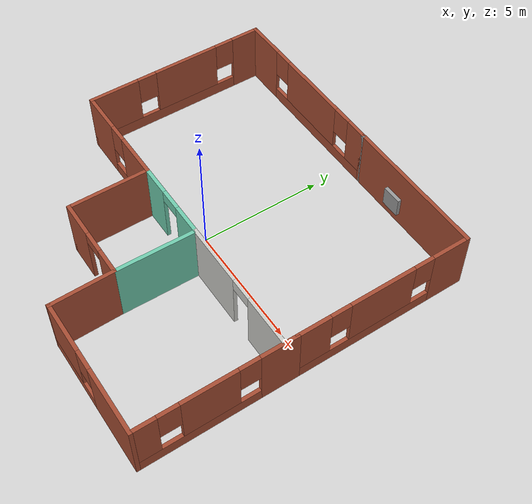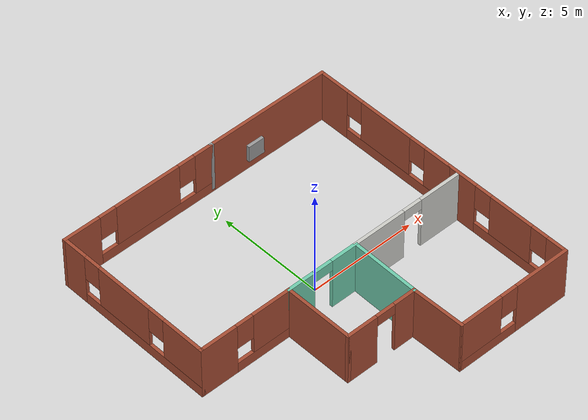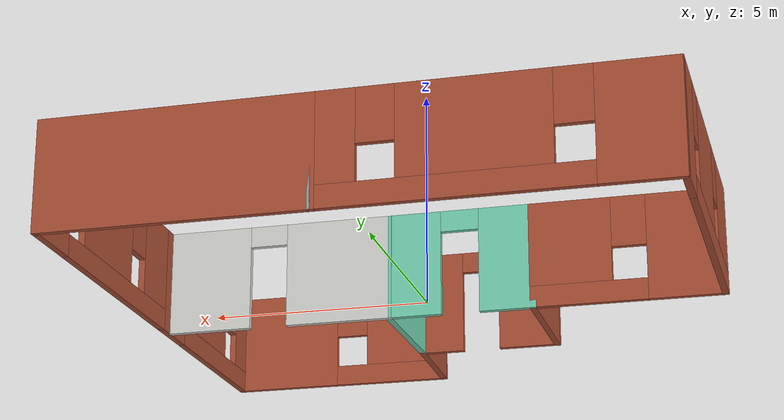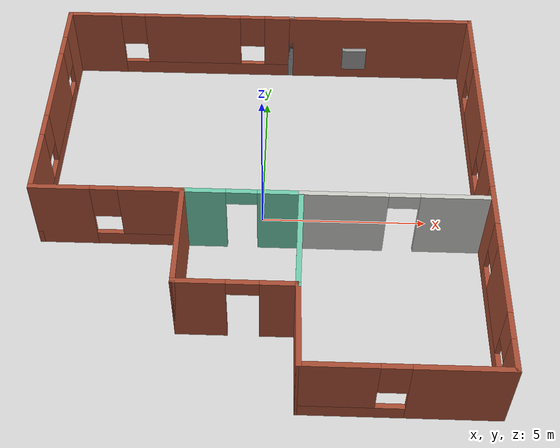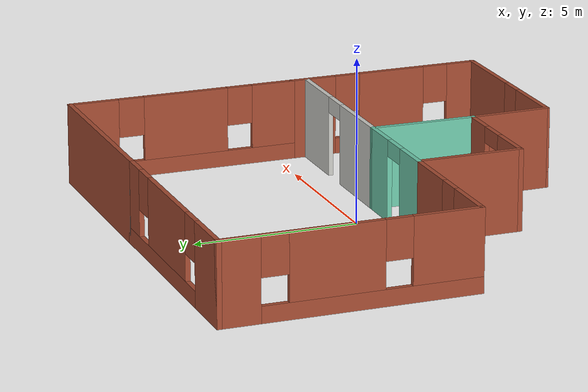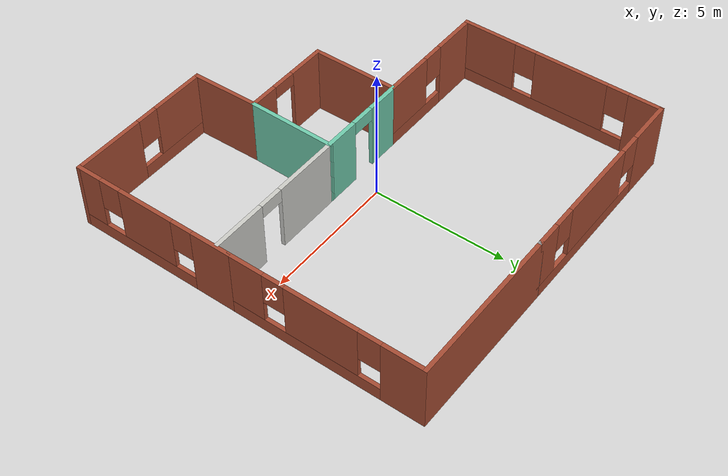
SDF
<?xml version='1.0'?>
<sdf version='1.6'>
  <model name='myWorld'>
    <link name='Wall_0'>
      <pose frame=''>-2.93 6.60073 0 0 -0 0</pose>
      <self_collide>0</self_collide>
      <enable_wind>0</enable_wind>
      <kinematic>0</kinematic>
      <visual name='Wall_0_Visual_0'>
        <pose frame=''>-2.87473 0 1.25 0 -0 0</pose>
        <geometry>
          <box>
            <size>1.75055 0.15 2.5</size>
          </box>
        </geometry>
        <material>
          <script>
            <uri>file://media/materials/scripts/gazebo.material</uri>
            <name>Gazebo/Bricks</name>
          </script>
          <ambient>1 1 1 1</ambient>
        </material>
        <meta>
          <layer>0</layer>
        </meta>
        <transparency>0</transparency>
        <cast_shadows>1</cast_shadows>
      </visual>
      <visual name='Wall_0_Visual_1'>
        <pose frame=''>0.875274 0 0.25 0 -0 0</pose>
        <geometry>
          <box>
            <size>5.74945 0.15 0.5</size>
          </box>
        </geometry>
        <material>
          <script>
            <uri>file://media/materials/scripts/gazebo.material</uri>
            <name>Gazebo/Bricks</name>
          </script>
          <ambient>1 1 1 1</ambient>
        </material>
        <meta>
          <layer>0</layer>
        </meta>
        <transparency>0</transparency>
        <cast_shadows>1</cast_shadows>
      </visual>
      <visual name='Wall_0_Visual_2'>
        <pose frame=''>0.388147 0 1.5 0 -0 0</pose>
        <geometry>
          <box>
            <size>3.1752 0.15 2</size>
          </box>
        </geometry>
        <material>
          <script>
            <uri>file://media/materials/scripts/gazebo.material</uri>
            <name>Gazebo/Bricks</name>
          </script>
          <ambient>1 1 1 1</ambient>
        </material>
        <meta>
          <layer>0</layer>
        </meta>
        <transparency>0</transparency>
        <cast_shadows>1</cast_shadows>
      </visual>
      <visual name='Wall_0_Visual_3'>
        <pose frame=''>3.26287 0 1.5 0 -0 0</pose>
        <geometry>
          <box>
            <size>0.974253 0.15 2</size>
          </box>
        </geometry>
        <material>
          <script>
            <uri>file://media/materials/scripts/gazebo.material</uri>
            <name>Gazebo/Bricks</name>
          </script>
          <ambient>1 1 1 1</ambient>
        </material>
        <meta>
          <layer>0</layer>
        </meta>
        <transparency>0</transparency>
        <cast_shadows>1</cast_shadows>
      </visual>
      <visual name='Wall_0_Visual_4'>
        <pose frame=''>-1.59945 0 1.9 0 -0 0</pose>
        <geometry>
          <box>
            <size>0.8 0.15 1.2</size>
          </box>
        </geometry>
        <material>
          <script>
            <uri>file://media/materials/scripts/gazebo.material</uri>
            <name>Gazebo/Bricks</name>
          </script>
          <ambient>1 1 1 1</ambient>
        </material>
        <meta>
          <layer>0</layer>
        </meta>
        <transparency>0</transparency>
        <cast_shadows>1</cast_shadows>
      </visual>
      <visual name='Wall_0_Visual_5'>
        <pose frame=''>2.37575 0 1.9 0 -0 0</pose>
        <geometry>
          <box>
            <size>0.8 0.15 1.2</size>
          </box>
        </geometry>
        <material>
          <script>
            <uri>file://media/materials/scripts/gazebo.material</uri>
            <name>Gazebo/Bricks</name>
          </script>
          <ambient>1 1 1 1</ambient>
        </material>
        <meta>
          <layer>0</layer>
        </meta>
        <transparency>0</transparency>
        <cast_shadows>1</cast_shadows>
      </visual>
      <collision name='Wall_0_Collision_2'>
        <laser_retro>0</laser_retro>
        <max_contacts>10</max_contacts>
        <pose frame=''>0.388147 0 1.5 0 -0 0</pose>
        <geometry>
          <box>
            <size>3.1752 0.15 2</size>
          </box>
        </geometry>
        <surface>
          <friction>
            <ode>
              <mu>1</mu>
              <mu2>1</mu2>
              <fdir1>0 0 0</fdir1>
              <slip1>0</slip1>
              <slip2>0</slip2>
            </ode>
            <torsional>
              <coefficient>1</coefficient>
              <patch_radius>0</patch_radius>
              <surface_radius>0</surface_radius>
              <use_patch_radius>1</use_patch_radius>
              <ode>
                <slip>0</slip>
              </ode>
            </torsional>
          </friction>
          <bounce>
            <restitution_coefficient>0</restitution_coefficient>
            <threshold>1e+06</threshold>
          </bounce>
          <contact>
            <collide_without_contact>0</collide_without_contact>
            <collide_without_contact_bitmask>1</collide_without_contact_bitmask>
            <collide_bitmask>1</collide_bitmask>
            <ode>
              <soft_cfm>0</soft_cfm>
              <soft_erp>0.2</soft_erp>
              <kp>1e+13</kp>
              <kd>1</kd>
              <max_vel>0.01</max_vel>
              <min_depth>0</min_depth>
            </ode>
            <bullet>
              <split_impulse>1</split_impulse>
              <split_impulse_penetration_threshold>-0.01</split_impulse_penetration_threshold>
              <soft_cfm>0</soft_cfm>
              <soft_erp>0.2</soft_erp>
              <kp>1e+13</kp>
              <kd>1</kd>
            </bullet>
          </contact>
        </surface>
      </collision>
      <collision name='Wall_0_Collision_0'>
        <laser_retro>0</laser_retro>
        <max_contacts>10</max_contacts>
        <pose frame=''>-2.87473 0 1.25 0 -0 0</pose>
        <geometry>
          <box>
            <size>1.75055 0.15 2.5</size>
          </box>
        </geometry>
        <surface>
          <friction>
            <ode>
              <mu>1</mu>
              <mu2>1</mu2>
              <fdir1>0 0 0</fdir1>
              <slip1>0</slip1>
              <slip2>0</slip2>
            </ode>
            <torsional>
              <coefficient>1</coefficient>
              <patch_radius>0</patch_radius>
              <surface_radius>0</surface_radius>
              <use_patch_radius>1</use_patch_radius>
              <ode>
                <slip>0</slip>
              </ode>
            </torsional>
          </friction>
          <bounce>
            <restitution_coefficient>0</restitution_coefficient>
            <threshold>1e+06</threshold>
          </bounce>
          <contact>
            <collide_without_contact>0</collide_without_contact>
            <collide_without_contact_bitmask>1</collide_without_contact_bitmask>
            <collide_bitmask>1</collide_bitmask>
            <ode>
              <soft_cfm>0</soft_cfm>
              <soft_erp>0.2</soft_erp>
              <kp>1e+13</kp>
              <kd>1</kd>
              <max_vel>0.01</max_vel>
              <min_depth>0</min_depth>
            </ode>
            <bullet>
              <split_impulse>1</split_impulse>
              <split_impulse_penetration_threshold>-0.01</split_impulse_penetration_threshold>
              <soft_cfm>0</soft_cfm>
              <soft_erp>0.2</soft_erp>
              <kp>1e+13</kp>
              <kd>1</kd>
            </bullet>
          </contact>
        </surface>
      </collision>
      <collision name='Wall_0_Collision_1'>
        <laser_retro>0</laser_retro>
        <max_contacts>10</max_contacts>
        <pose frame=''>0.875274 0 0.25 0 -0 0</pose>
        <geometry>
          <box>
            <size>5.74945 0.15 0.5</size>
          </box>
        </geometry>
        <surface>
          <friction>
            <ode>
              <mu>1</mu>
              <mu2>1</mu2>
              <fdir1>0 0 0</fdir1>
              <slip1>0</slip1>
              <slip2>0</slip2>
            </ode>
            <torsional>
              <coefficient>1</coefficient>
              <patch_radius>0</patch_radius>
              <surface_radius>0</surface_radius>
              <use_patch_radius>1</use_patch_radius>
              <ode>
                <slip>0</slip>
              </ode>
            </torsional>
          </friction>
          <bounce>
            <restitution_coefficient>0</restitution_coefficient>
            <threshold>1e+06</threshold>
          </bounce>
          <contact>
            <collide_without_contact>0</collide_without_contact>
            <collide_without_contact_bitmask>1</collide_without_contact_bitmask>
            <collide_bitmask>1</collide_bitmask>
            <ode>
              <soft_cfm>0</soft_cfm>
              <soft_erp>0.2</soft_erp>
              <kp>1e+13</kp>
              <kd>1</kd>
              <max_vel>0.01</max_vel>
              <min_depth>0</min_depth>
            </ode>
            <bullet>
              <split_impulse>1</split_impulse>
              <split_impulse_penetration_threshold>-0.01</split_impulse_penetration_threshold>
              <soft_cfm>0</soft_cfm>
              <soft_erp>0.2</soft_erp>
              <kp>1e+13</kp>
              <kd>1</kd>
            </bullet>
          </contact>
        </surface>
      </collision>
      <collision name='Wall_0_Collision_3'>
        <laser_retro>0</laser_retro>
        <max_contacts>10</max_contacts>
        <pose frame=''>3.26287 0 1.5 0 -0 0</pose>
        <geometry>
          <box>
            <size>0.974253 0.15 2</size>
          </box>
        </geometry>
        <surface>
          <friction>
            <ode>
              <mu>1</mu>
              <mu2>1</mu2>
              <fdir1>0 0 0</fdir1>
              <slip1>0</slip1>
              <slip2>0</slip2>
            </ode>
            <torsional>
              <coefficient>1</coefficient>
              <patch_radius>0</patch_radius>
              <surface_radius>0</surface_radius>
              <use_patch_radius>1</use_patch_radius>
              <ode>
                <slip>0</slip>
              </ode>
            </torsional>
          </friction>
          <bounce>
            <restitution_coefficient>0</restitution_coefficient>
            <threshold>1e+06</threshold>
          </bounce>
          <contact>
            <collide_without_contact>0</collide_without_contact>
            <collide_without_contact_bitmask>1</collide_without_contact_bitmask>
            <collide_bitmask>1</collide_bitmask>
            <ode>
              <soft_cfm>0</soft_cfm>
              <soft_erp>0.2</soft_erp>
              <kp>1e+13</kp>
              <kd>1</kd>
              <max_vel>0.01</max_vel>
              <min_depth>0</min_depth>
            </ode>
            <bullet>
              <split_impulse>1</split_impulse>
              <split_impulse_penetration_threshold>-0.01</split_impulse_penetration_threshold>
              <soft_cfm>0</soft_cfm>
              <soft_erp>0.2</soft_erp>
              <kp>1e+13</kp>
              <kd>1</kd>
            </bullet>
          </contact>
        </surface>
      </collision>
      <collision name='Wall_0_Collision_4'>
        <laser_retro>0</laser_retro>
        <max_contacts>10</max_contacts>
        <pose frame=''>-1.59945 0 1.9 0 -0 0</pose>
        <geometry>
          <box>
            <size>0.8 0.15 1.2</size>
          </box>
        </geometry>
        <surface>
          <friction>
            <ode>
              <mu>1</mu>
              <mu2>1</mu2>
              <fdir1>0 0 0</fdir1>
              <slip1>0</slip1>
              <slip2>0</slip2>
            </ode>
            <torsional>
              <coefficient>1</coefficient>
              <patch_radius>0</patch_radius>
              <surface_radius>0</surface_radius>
              <use_patch_radius>1</use_patch_radius>
              <ode>
                <slip>0</slip>
              </ode>
            </torsional>
          </friction>
          <bounce>
            <restitution_coefficient>0</restitution_coefficient>
            <threshold>1e+06</threshold>
          </bounce>
          <contact>
            <collide_without_contact>0</collide_without_contact>
            <collide_without_contact_bitmask>1</collide_without_contact_bitmask>
            <collide_bitmask>1</collide_bitmask>
            <ode>
              <soft_cfm>0</soft_cfm>
              <soft_erp>0.2</soft_erp>
              <kp>1e+13</kp>
              <kd>1</kd>
              <max_vel>0.01</max_vel>
              <min_depth>0</min_depth>
            </ode>
            <bullet>
              <split_impulse>1</split_impulse>
              <split_impulse_penetration_threshold>-0.01</split_impulse_penetration_threshold>
              <soft_cfm>0</soft_cfm>
              <soft_erp>0.2</soft_erp>
              <kp>1e+13</kp>
              <kd>1</kd>
            </bullet>
          </contact>
        </surface>
      </collision>
      <collision name='Wall_0_Collision_5'>
        <laser_retro>0</laser_retro>
        <max_contacts>10</max_contacts>
        <pose frame=''>2.37575 0 1.9 0 -0 0</pose>
        <geometry>
          <box>
            <size>0.8 0.15 1.2</size>
          </box>
        </geometry>
        <surface>
          <friction>
            <ode>
              <mu>1</mu>
              <mu2>1</mu2>
              <fdir1>0 0 0</fdir1>
              <slip1>0</slip1>
              <slip2>0</slip2>
            </ode>
            <torsional>
              <coefficient>1</coefficient>
              <patch_radius>0</patch_radius>
              <surface_radius>0</surface_radius>
              <use_patch_radius>1</use_patch_radius>
              <ode>
                <slip>0</slip>
              </ode>
            </torsional>
          </friction>
          <bounce>
            <restitution_coefficient>0</restitution_coefficient>
            <threshold>1e+06</threshold>
          </bounce>
          <contact>
            <collide_without_contact>0</collide_without_contact>
            <collide_without_contact_bitmask>1</collide_without_contact_bitmask>
            <collide_bitmask>1</collide_bitmask>
            <ode>
              <soft_cfm>0</soft_cfm>
              <soft_erp>0.2</soft_erp>
              <kp>1e+13</kp>
              <kd>1</kd>
              <max_vel>0.01</max_vel>
              <min_depth>0</min_depth>
            </ode>
            <bullet>
              <split_impulse>1</split_impulse>
              <split_impulse_penetration_threshold>-0.01</split_impulse_penetration_threshold>
              <soft_cfm>0</soft_cfm>
              <soft_erp>0.2</soft_erp>
              <kp>1e+13</kp>
              <kd>1</kd>
            </bullet>
          </contact>
        </surface>
      </collision>
    </link>
    <link name='Wall_1'>
      <pose frame=''>0.75 6.60073 0 0 -0 0</pose>
      <self_collide>0</self_collide>
      <enable_wind>0</enable_wind>
      <kinematic>0</kinematic>
      <visual name='Wall_1_Visual'>
        <pose frame=''>0 0 1.25 0 -0 0</pose>
        <geometry>
          <box>
            <size>0.16 0.15 2.5</size>
          </box>
        </geometry>
        <material>
          <script>
            <uri>file://media/materials/scripts/gazebo.material</uri>
            <name>Gazebo/Grey</name>
          </script>
          <ambient>1 1 1 1</ambient>
        </material>
        <meta>
          <layer>0</layer>
        </meta>
        <transparency>0</transparency>
        <cast_shadows>1</cast_shadows>
      </visual>
      <collision name='Wall_1_Collision'>
        <laser_retro>0</laser_retro>
        <max_contacts>10</max_contacts>
        <pose frame=''>0 0 1.25 0 -0 0</pose>
        <geometry>
          <box>
            <size>0.16 0.15 2.5</size>
          </box>
        </geometry>
        <surface>
          <friction>
            <ode>
              <mu>1</mu>
              <mu2>1</mu2>
              <fdir1>0 0 0</fdir1>
              <slip1>0</slip1>
              <slip2>0</slip2>
            </ode>
            <torsional>
              <coefficient>1</coefficient>
              <patch_radius>0</patch_radius>
              <surface_radius>0</surface_radius>
              <use_patch_radius>1</use_patch_radius>
              <ode>
                <slip>0</slip>
              </ode>
            </torsional>
          </friction>
          <bounce>
            <restitution_coefficient>0</restitution_coefficient>
            <threshold>1e+06</threshold>
          </bounce>
          <contact>
            <collide_without_contact>0</collide_without_contact>
            <collide_without_contact_bitmask>1</collide_without_contact_bitmask>
            <collide_bitmask>1</collide_bitmask>
            <ode>
              <soft_cfm>0</soft_cfm>
              <soft_erp>0.2</soft_erp>
              <kp>1e+13</kp>
              <kd>1</kd>
              <max_vel>0.01</max_vel>
              <min_depth>0</min_depth>
            </ode>
            <bullet>
              <split_impulse>1</split_impulse>
              <split_impulse_penetration_threshold>-0.01</split_impulse_penetration_threshold>
              <soft_cfm>0</soft_cfm>
              <soft_erp>0.2</soft_erp>
              <kp>1e+13</kp>
              <kd>1</kd>
            </bullet>
          </contact>
        </surface>
      </collision>
    </link>
    <link name='Wall_11'>
      <pose frame=''>3.88 -6.59927 0 0 -0 3.14159</pose>
      <self_collide>0</self_collide>
      <enable_wind>0</enable_wind>
      <kinematic>0</kinematic>
      <visual name='Wall_11_Visual_0'>
        <pose frame=''>-1.45842 0 1.25 0 -0 0</pose>
        <geometry>
          <box>
            <size>2.68316 0.15 2.5</size>
          </box>
        </geometry>
        <material>
          <script>
            <uri>file://media/materials/scripts/gazebo.material</uri>
            <name>Gazebo/Bricks</name>
          </script>
          <ambient>1 1 1 1</ambient>
        </material>
        <meta>
          <layer>0</layer>
        </meta>
        <transparency>0</transparency>
        <cast_shadows>1</cast_shadows>
      </visual>
      <visual name='Wall_11_Visual_1'>
        <pose frame=''>1.34158 0 0.25 0 -0 0</pose>
        <geometry>
          <box>
            <size>2.91684 0.15 0.5</size>
          </box>
        </geometry>
        <material>
          <script>
            <uri>file://media/materials/scripts/gazebo.material</uri>
            <name>Gazebo/Bricks</name>
          </script>
          <ambient>1 1 1 1</ambient>
        </material>
        <meta>
          <layer>0</layer>
        </meta>
        <transparency>0</transparency>
        <cast_shadows>1</cast_shadows>
      </visual>
      <visual name='Wall_11_Visual_2'>
        <pose frame=''>1.74158 0 1.5 0 -0 0</pose>
        <geometry>
          <box>
            <size>2.11684 0.15 2</size>
          </box>
        </geometry>
        <material>
          <script>
            <uri>file://media/materials/scripts/gazebo.material</uri>
            <name>Gazebo/Bricks</name>
          </script>
          <ambient>1 1 1 1</ambient>
        </material>
        <meta>
          <layer>0</layer>
        </meta>
        <transparency>0</transparency>
        <cast_shadows>1</cast_shadows>
      </visual>
      <visual name='Wall_11_Visual_3'>
        <pose frame=''>0.283159 0 1.9 0 -0 0</pose>
        <geometry>
          <box>
            <size>0.8 0.15 1.2</size>
          </box>
        </geometry>
        <material>
          <script>
            <uri>file://media/materials/scripts/gazebo.material</uri>
            <name>Gazebo/Bricks</name>
          </script>
          <ambient>1 1 1 1</ambient>
        </material>
        <meta>
          <layer>0</layer>
        </meta>
        <transparency>0</transparency>
        <cast_shadows>1</cast_shadows>
      </visual>
      <collision name='Wall_11_Collision_0'>
        <laser_retro>0</laser_retro>
        <max_contacts>10</max_contacts>
        <pose frame=''>-1.45842 0 1.25 0 -0 0</pose>
        <geometry>
          <box>
            <size>2.68316 0.15 2.5</size>
          </box>
        </geometry>
        <surface>
          <friction>
            <ode>
              <mu>1</mu>
              <mu2>1</mu2>
              <fdir1>0 0 0</fdir1>
              <slip1>0</slip1>
              <slip2>0</slip2>
            </ode>
            <torsional>
              <coefficient>1</coefficient>
              <patch_radius>0</patch_radius>
              <surface_radius>0</surface_radius>
              <use_patch_radius>1</use_patch_radius>
              <ode>
                <slip>0</slip>
              </ode>
            </torsional>
          </friction>
          <bounce>
            <restitution_coefficient>0</restitution_coefficient>
            <threshold>1e+06</threshold>
          </bounce>
          <contact>
            <collide_without_contact>0</collide_without_contact>
            <collide_without_contact_bitmask>1</collide_without_contact_bitmask>
            <collide_bitmask>1</collide_bitmask>
            <ode>
              <soft_cfm>0</soft_cfm>
              <soft_erp>0.2</soft_erp>
              <kp>1e+13</kp>
              <kd>1</kd>
              <max_vel>0.01</max_vel>
              <min_depth>0</min_depth>
            </ode>
            <bullet>
              <split_impulse>1</split_impulse>
              <split_impulse_penetration_threshold>-0.01</split_impulse_penetration_threshold>
              <soft_cfm>0</soft_cfm>
              <soft_erp>0.2</soft_erp>
              <kp>1e+13</kp>
              <kd>1</kd>
            </bullet>
          </contact>
        </surface>
      </collision>
      <collision name='Wall_11_Collision_1'>
        <laser_retro>0</laser_retro>
        <max_contacts>10</max_contacts>
        <pose frame=''>1.34158 0 0.25 0 -0 0</pose>
        <geometry>
          <box>
            <size>2.91684 0.15 0.5</size>
          </box>
        </geometry>
        <surface>
          <friction>
            <ode>
              <mu>1</mu>
              <mu2>1</mu2>
              <fdir1>0 0 0</fdir1>
              <slip1>0</slip1>
              <slip2>0</slip2>
            </ode>
            <torsional>
              <coefficient>1</coefficient>
              <patch_radius>0</patch_radius>
              <surface_radius>0</surface_radius>
              <use_patch_radius>1</use_patch_radius>
              <ode>
                <slip>0</slip>
              </ode>
            </torsional>
          </friction>
          <bounce>
            <restitution_coefficient>0</restitution_coefficient>
            <threshold>1e+06</threshold>
          </bounce>
          <contact>
            <collide_without_contact>0</collide_without_contact>
            <collide_without_contact_bitmask>1</collide_without_contact_bitmask>
            <collide_bitmask>1</collide_bitmask>
            <ode>
              <soft_cfm>0</soft_cfm>
              <soft_erp>0.2</soft_erp>
              <kp>1e+13</kp>
              <kd>1</kd>
              <max_vel>0.01</max_vel>
              <min_depth>0</min_depth>
            </ode>
            <bullet>
              <split_impulse>1</split_impulse>
              <split_impulse_penetration_threshold>-0.01</split_impulse_penetration_threshold>
              <soft_cfm>0</soft_cfm>
              <soft_erp>0.2</soft_erp>
              <kp>1e+13</kp>
              <kd>1</kd>
            </bullet>
          </contact>
        </surface>
      </collision>
      <collision name='Wall_11_Collision_2'>
        <laser_retro>0</laser_retro>
        <max_contacts>10</max_contacts>
        <pose frame=''>1.74158 0 1.5 0 -0 0</pose>
        <geometry>
          <box>
            <size>2.11684 0.15 2</size>
          </box>
        </geometry>
        <surface>
          <friction>
            <ode>
              <mu>1</mu>
              <mu2>1</mu2>
              <fdir1>0 0 0</fdir1>
              <slip1>0</slip1>
              <slip2>0</slip2>
            </ode>
            <torsional>
              <coefficient>1</coefficient>
              <patch_radius>0</patch_radius>
              <surface_radius>0</surface_radius>
              <use_patch_radius>1</use_patch_radius>
              <ode>
                <slip>0</slip>
              </ode>
            </torsional>
          </friction>
          <bounce>
            <restitution_coefficient>0</restitution_coefficient>
            <threshold>1e+06</threshold>
          </bounce>
          <contact>
            <collide_without_contact>0</collide_without_contact>
            <collide_without_contact_bitmask>1</collide_without_contact_bitmask>
            <collide_bitmask>1</collide_bitmask>
            <ode>
              <soft_cfm>0</soft_cfm>
              <soft_erp>0.2</soft_erp>
              <kp>1e+13</kp>
              <kd>1</kd>
              <max_vel>0.01</max_vel>
              <min_depth>0</min_depth>
            </ode>
            <bullet>
              <split_impulse>1</split_impulse>
              <split_impulse_penetration_threshold>-0.01</split_impulse_penetration_threshold>
              <soft_cfm>0</soft_cfm>
              <soft_erp>0.2</soft_erp>
              <kp>1e+13</kp>
              <kd>1</kd>
            </bullet>
          </contact>
        </surface>
      </collision>
      <collision name='Wall_11_Collision_3'>
        <laser_retro>0</laser_retro>
        <max_contacts>10</max_contacts>
        <pose frame=''>0.283159 0 1.9 0 -0 0</pose>
        <geometry>
          <box>
            <size>0.8 0.15 1.2</size>
          </box>
        </geometry>
        <surface>
          <friction>
            <ode>
              <mu>1</mu>
              <mu2>1</mu2>
              <fdir1>0 0 0</fdir1>
              <slip1>0</slip1>
              <slip2>0</slip2>
            </ode>
            <torsional>
              <coefficient>1</coefficient>
              <patch_radius>0</patch_radius>
              <surface_radius>0</surface_radius>
              <use_patch_radius>1</use_patch_radius>
              <ode>
                <slip>0</slip>
              </ode>
            </torsional>
          </friction>
          <bounce>
            <restitution_coefficient>0</restitution_coefficient>
            <threshold>1e+06</threshold>
          </bounce>
          <contact>
            <collide_without_contact>0</collide_without_contact>
            <collide_without_contact_bitmask>1</collide_without_contact_bitmask>
            <collide_bitmask>1</collide_bitmask>
            <ode>
              <soft_cfm>0</soft_cfm>
              <soft_erp>0.2</soft_erp>
              <kp>1e+13</kp>
              <kd>1</kd>
              <max_vel>0.01</max_vel>
              <min_depth>0</min_depth>
            </ode>
            <bullet>
              <split_impulse>1</split_impulse>
              <split_impulse_penetration_threshold>-0.01</split_impulse_penetration_threshold>
              <soft_cfm>0</soft_cfm>
              <soft_erp>0.2</soft_erp>
              <kp>1e+13</kp>
              <kd>1</kd>
            </bullet>
          </contact>
        </surface>
      </collision>
    </link>
    <link name='Wall_2'>
      <pose frame=''>3.68 6.60073 0 0 -0 0</pose>
      <self_collide>0</self_collide>
      <enable_wind>0</enable_wind>
      <kinematic>0</kinematic>
      <visual name='Wall_2_Visual'>
        <pose frame=''>0 0 1.25 0 -0 0</pose>
        <geometry>
          <box>
            <size>6 0.15 2.5</size>
          </box>
        </geometry>
        <material>
          <script>
            <uri>file://media/materials/scripts/gazebo.material</uri>
            <name>Gazebo/Bricks</name>
          </script>
          <ambient>1 1 1 1</ambient>
        </material>
        <meta>
          <layer>0</layer>
        </meta>
        <transparency>0</transparency>
        <cast_shadows>1</cast_shadows>
      </visual>
      <collision name='Wall_2_Collision'>
        <laser_retro>0</laser_retro>
        <max_contacts>10</max_contacts>
        <pose frame=''>0 0 1.25 0 -0 0</pose>
        <geometry>
          <box>
            <size>6 0.15 2.5</size>
          </box>
        </geometry>
        <surface>
          <friction>
            <ode>
              <mu>1</mu>
              <mu2>1</mu2>
              <fdir1>0 0 0</fdir1>
              <slip1>0</slip1>
              <slip2>0</slip2>
            </ode>
            <torsional>
              <coefficient>1</coefficient>
              <patch_radius>0</patch_radius>
              <surface_radius>0</surface_radius>
              <use_patch_radius>1</use_patch_radius>
              <ode>
                <slip>0</slip>
              </ode>
            </torsional>
          </friction>
          <bounce>
            <restitution_coefficient>0</restitution_coefficient>
            <threshold>1e+06</threshold>
          </bounce>
          <contact>
            <collide_without_contact>0</collide_without_contact>
            <collide_without_contact_bitmask>1</collide_without_contact_bitmask>
            <collide_bitmask>1</collide_bitmask>
            <ode>
              <soft_cfm>0</soft_cfm>
              <soft_erp>0.2</soft_erp>
              <kp>1e+13</kp>
              <kd>1</kd>
              <max_vel>0.01</max_vel>
              <min_depth>0</min_depth>
            </ode>
            <bullet>
              <split_impulse>1</split_impulse>
              <split_impulse_penetration_threshold>-0.01</split_impulse_penetration_threshold>
              <soft_cfm>0</soft_cfm>
              <soft_erp>0.2</soft_erp>
              <kp>1e+13</kp>
              <kd>1</kd>
            </bullet>
          </contact>
        </surface>
      </collision>
    </link>
    <link name='Wall_24'>
      <pose frame=''>-6.605 2.80073 0 0 0 -1.5708</pose>
      <self_collide>0</self_collide>
      <enable_wind>0</enable_wind>
      <kinematic>0</kinematic>
      <visual name='Wall_24_Visual_0'>
        <pose frame=''>-3.24598 0 1.25 0 -0 0</pose>
        <geometry>
          <box>
            <size>1.25804 0.15 2.5</size>
          </box>
        </geometry>
        <material>
          <script>
            <uri>file://media/materials/scripts/gazebo.material</uri>
            <name>Gazebo/Bricks</name>
          </script>
          <ambient>1 1 1 1</ambient>
        </material>
        <meta>
          <layer>0</layer>
        </meta>
        <transparency>0</transparency>
        <cast_shadows>1</cast_shadows>
      </visual>
      <visual name='Wall_24_Visual_1'>
        <pose frame=''>0.629022 0 0.25 0 -0 0</pose>
        <geometry>
          <box>
            <size>6.49196 0.15 0.5</size>
          </box>
        </geometry>
        <material>
          <script>
            <uri>file://media/materials/scripts/gazebo.material</uri>
            <name>Gazebo/Bricks</name>
          </script>
          <ambient>1 1 1 1</ambient>
        </material>
        <meta>
          <layer>0</layer>
        </meta>
        <transparency>0</transparency>
        <cast_shadows>1</cast_shadows>
      </visual>
      <visual name='Wall_24_Visual_2'>
        <pose frame=''>-0.422839 0 1.5 0 -0 0</pose>
        <geometry>
          <box>
            <size>2.78823 0.15 2</size>
          </box>
        </geometry>
        <material>
          <script>
            <uri>file://media/materials/scripts/gazebo.material</uri>
            <name>Gazebo/Bricks</name>
          </script>
          <ambient>1 1 1 1</ambient>
        </material>
        <meta>
          <layer>0</layer>
        </meta>
        <transparency>0</transparency>
        <cast_shadows>1</cast_shadows>
      </visual>
      <visual name='Wall_24_Visual_3'>
        <pose frame=''>2.82314 0 1.5 0 -0 0</pose>
        <geometry>
          <box>
            <size>2.10372 0.15 2</size>
          </box>
        </geometry>
        <material>
          <script>
            <uri>file://media/materials/scripts/gazebo.material</uri>
            <name>Gazebo/Bricks</name>
          </script>
          <ambient>1 1 1 1</ambient>
        </material>
        <meta>
          <layer>0</layer>
        </meta>
        <transparency>0</transparency>
        <cast_shadows>1</cast_shadows>
      </visual>
      <visual name='Wall_24_Visual_4'>
        <pose frame=''>-2.21696 0 1.9 0 -0 0</pose>
        <geometry>
          <box>
            <size>0.8 0.15 1.2</size>
          </box>
        </geometry>
        <material>
          <script>
            <uri>file://media/materials/scripts/gazebo.material</uri>
            <name>Gazebo/Bricks</name>
          </script>
          <ambient>1 1 1 1</ambient>
        </material>
        <meta>
          <layer>0</layer>
        </meta>
        <transparency>0</transparency>
        <cast_shadows>1</cast_shadows>
      </visual>
      <visual name='Wall_24_Visual_5'>
        <pose frame=''>1.37128 0 1.9 0 -0 0</pose>
        <geometry>
          <box>
            <size>0.8 0.15 1.2</size>
          </box>
        </geometry>
        <material>
          <script>
            <uri>file://media/materials/scripts/gazebo.material</uri>
            <name>Gazebo/Bricks</name>
          </script>
          <ambient>1 1 1 1</ambient>
        </material>
        <meta>
          <layer>0</layer>
        </meta>
        <transparency>0</transparency>
        <cast_shadows>1</cast_shadows>
      </visual>
      <collision name='Wall_24_Collision_0'>
        <laser_retro>0</laser_retro>
        <max_contacts>10</max_contacts>
        <pose frame=''>-3.24598 0 1.25 0 -0 0</pose>
        <geometry>
          <box>
            <size>1.25804 0.15 2.5</size>
          </box>
        </geometry>
        <surface>
          <friction>
            <ode>
              <mu>1</mu>
              <mu2>1</mu2>
              <fdir1>0 0 0</fdir1>
              <slip1>0</slip1>
              <slip2>0</slip2>
            </ode>
            <torsional>
              <coefficient>1</coefficient>
              <patch_radius>0</patch_radius>
              <surface_radius>0</surface_radius>
              <use_patch_radius>1</use_patch_radius>
              <ode>
                <slip>0</slip>
              </ode>
            </torsional>
          </friction>
          <bounce>
            <restitution_coefficient>0</restitution_coefficient>
            <threshold>1e+06</threshold>
          </bounce>
          <contact>
            <collide_without_contact>0</collide_without_contact>
            <collide_without_contact_bitmask>1</collide_without_contact_bitmask>
            <collide_bitmask>1</collide_bitmask>
            <ode>
              <soft_cfm>0</soft_cfm>
              <soft_erp>0.2</soft_erp>
              <kp>1e+13</kp>
              <kd>1</kd>
              <max_vel>0.01</max_vel>
              <min_depth>0</min_depth>
            </ode>
            <bullet>
              <split_impulse>1</split_impulse>
              <split_impulse_penetration_threshold>-0.01</split_impulse_penetration_threshold>
              <soft_cfm>0</soft_cfm>
              <soft_erp>0.2</soft_erp>
              <kp>1e+13</kp>
              <kd>1</kd>
            </bullet>
          </contact>
        </surface>
      </collision>
      <collision name='Wall_24_Collision_1'>
        <laser_retro>0</laser_retro>
        <max_contacts>10</max_contacts>
        <pose frame=''>0.629022 0 0.25 0 -0 0</pose>
        <geometry>
          <box>
            <size>6.49196 0.15 0.5</size>
          </box>
        </geometry>
        <surface>
          <friction>
            <ode>
              <mu>1</mu>
              <mu2>1</mu2>
              <fdir1>0 0 0</fdir1>
              <slip1>0</slip1>
              <slip2>0</slip2>
            </ode>
            <torsional>
              <coefficient>1</coefficient>
              <patch_radius>0</patch_radius>
              <surface_radius>0</surface_radius>
              <use_patch_radius>1</use_patch_radius>
              <ode>
                <slip>0</slip>
              </ode>
            </torsional>
          </friction>
          <bounce>
            <restitution_coefficient>0</restitution_coefficient>
            <threshold>1e+06</threshold>
          </bounce>
          <contact>
            <collide_without_contact>0</collide_without_contact>
            <collide_without_contact_bitmask>1</collide_without_contact_bitmask>
            <collide_bitmask>1</collide_bitmask>
            <ode>
              <soft_cfm>0</soft_cfm>
              <soft_erp>0.2</soft_erp>
              <kp>1e+13</kp>
              <kd>1</kd>
              <max_vel>0.01</max_vel>
              <min_depth>0</min_depth>
            </ode>
            <bullet>
              <split_impulse>1</split_impulse>
              <split_impulse_penetration_threshold>-0.01</split_impulse_penetration_threshold>
              <soft_cfm>0</soft_cfm>
              <soft_erp>0.2</soft_erp>
              <kp>1e+13</kp>
              <kd>1</kd>
            </bullet>
          </contact>
        </surface>
      </collision>
      <collision name='Wall_24_Collision_2'>
        <laser_retro>0</laser_retro>
        <max_contacts>10</max_contacts>
        <pose frame=''>-0.422839 0 1.5 0 -0 0</pose>
        <geometry>
          <box>
            <size>2.78823 0.15 2</size>
          </box>
        </geometry>
        <surface>
          <friction>
            <ode>
              <mu>1</mu>
              <mu2>1</mu2>
              <fdir1>0 0 0</fdir1>
              <slip1>0</slip1>
              <slip2>0</slip2>
            </ode>
            <torsional>
              <coefficient>1</coefficient>
              <patch_radius>0</patch_radius>
              <surface_radius>0</surface_radius>
              <use_patch_radius>1</use_patch_radius>
              <ode>
                <slip>0</slip>
              </ode>
            </torsional>
          </friction>
          <bounce>
            <restitution_coefficient>0</restitution_coefficient>
            <threshold>1e+06</threshold>
          </bounce>
          <contact>
            <collide_without_contact>0</collide_without_contact>
            <collide_without_contact_bitmask>1</collide_without_contact_bitmask>
            <collide_bitmask>1</collide_bitmask>
            <ode>
              <soft_cfm>0</soft_cfm>
              <soft_erp>0.2</soft_erp>
              <kp>1e+13</kp>
              <kd>1</kd>
              <max_vel>0.01</max_vel>
              <min_depth>0</min_depth>
            </ode>
            <bullet>
              <split_impulse>1</split_impulse>
              <split_impulse_penetration_threshold>-0.01</split_impulse_penetration_threshold>
              <soft_cfm>0</soft_cfm>
              <soft_erp>0.2</soft_erp>
              <kp>1e+13</kp>
              <kd>1</kd>
            </bullet>
          </contact>
        </surface>
      </collision>
      <collision name='Wall_24_Collision_3'>
        <laser_retro>0</laser_retro>
        <max_contacts>10</max_contacts>
        <pose frame=''>2.82314 0 1.5 0 -0 0</pose>
        <geometry>
          <box>
            <size>2.10372 0.15 2</size>
          </box>
        </geometry>
        <surface>
          <friction>
            <ode>
              <mu>1</mu>
              <mu2>1</mu2>
              <fdir1>0 0 0</fdir1>
              <slip1>0</slip1>
              <slip2>0</slip2>
            </ode>
            <torsional>
              <coefficient>1</coefficient>
              <patch_radius>0</patch_radius>
              <surface_radius>0</surface_radius>
              <use_patch_radius>1</use_patch_radius>
              <ode>
                <slip>0</slip>
              </ode>
            </torsional>
          </friction>
          <bounce>
            <restitution_coefficient>0</restitution_coefficient>
            <threshold>1e+06</threshold>
          </bounce>
          <contact>
            <collide_without_contact>0</collide_without_contact>
            <collide_without_contact_bitmask>1</collide_without_contact_bitmask>
            <collide_bitmask>1</collide_bitmask>
            <ode>
              <soft_cfm>0</soft_cfm>
              <soft_erp>0.2</soft_erp>
              <kp>1e+13</kp>
              <kd>1</kd>
              <max_vel>0.01</max_vel>
              <min_depth>0</min_depth>
            </ode>
            <bullet>
              <split_impulse>1</split_impulse>
              <split_impulse_penetration_threshold>-0.01</split_impulse_penetration_threshold>
              <soft_cfm>0</soft_cfm>
              <soft_erp>0.2</soft_erp>
              <kp>1e+13</kp>
              <kd>1</kd>
            </bullet>
          </contact>
        </surface>
      </collision>
      <collision name='Wall_24_Collision_4'>
        <laser_retro>0</laser_retro>
        <max_contacts>10</max_contacts>
        <pose frame=''>-2.21696 0 1.9 0 -0 0</pose>
        <geometry>
          <box>
            <size>0.8 0.15 1.2</size>
          </box>
        </geometry>
        <surface>
          <friction>
            <ode>
              <mu>1</mu>
              <mu2>1</mu2>
              <fdir1>0 0 0</fdir1>
              <slip1>0</slip1>
              <slip2>0</slip2>
            </ode>
            <torsional>
              <coefficient>1</coefficient>
              <patch_radius>0</patch_radius>
              <surface_radius>0</surface_radius>
              <use_patch_radius>1</use_patch_radius>
              <ode>
                <slip>0</slip>
              </ode>
            </torsional>
          </friction>
          <bounce>
            <restitution_coefficient>0</restitution_coefficient>
            <threshold>1e+06</threshold>
          </bounce>
          <contact>
            <collide_without_contact>0</collide_without_contact>
            <collide_without_contact_bitmask>1</collide_without_contact_bitmask>
            <collide_bitmask>1</collide_bitmask>
            <ode>
              <soft_cfm>0</soft_cfm>
              <soft_erp>0.2</soft_erp>
              <kp>1e+13</kp>
              <kd>1</kd>
              <max_vel>0.01</max_vel>
              <min_depth>0</min_depth>
            </ode>
            <bullet>
              <split_impulse>1</split_impulse>
              <split_impulse_penetration_threshold>-0.01</split_impulse_penetration_threshold>
              <soft_cfm>0</soft_cfm>
              <soft_erp>0.2</soft_erp>
              <kp>1e+13</kp>
              <kd>1</kd>
            </bullet>
          </contact>
        </surface>
      </collision>
      <collision name='Wall_24_Collision_5'>
        <laser_retro>0</laser_retro>
        <max_contacts>10</max_contacts>
        <pose frame=''>1.37128 0 1.9 0 -0 0</pose>
        <geometry>
          <box>
            <size>0.8 0.15 1.2</size>
          </box>
        </geometry>
        <surface>
          <friction>
            <ode>
              <mu>1</mu>
              <mu2>1</mu2>
              <fdir1>0 0 0</fdir1>
              <slip1>0</slip1>
              <slip2>0</slip2>
            </ode>
            <torsional>
              <coefficient>1</coefficient>
              <patch_radius>0</patch_radius>
              <surface_radius>0</surface_radius>
              <use_patch_radius>1</use_patch_radius>
              <ode>
                <slip>0</slip>
              </ode>
            </torsional>
          </friction>
          <bounce>
            <restitution_coefficient>0</restitution_coefficient>
            <threshold>1e+06</threshold>
          </bounce>
          <contact>
            <collide_without_contact>0</collide_without_contact>
            <collide_without_contact_bitmask>1</collide_without_contact_bitmask>
            <collide_bitmask>1</collide_bitmask>
            <ode>
              <soft_cfm>0</soft_cfm>
              <soft_erp>0.2</soft_erp>
              <kp>1e+13</kp>
              <kd>1</kd>
              <max_vel>0.01</max_vel>
              <min_depth>0</min_depth>
            </ode>
            <bullet>
              <split_impulse>1</split_impulse>
              <split_impulse_penetration_threshold>-0.01</split_impulse_penetration_threshold>
              <soft_cfm>0</soft_cfm>
              <soft_erp>0.2</soft_erp>
              <kp>1e+13</kp>
              <kd>1</kd>
            </bullet>
          </contact>
        </surface>
      </collision>
    </link>
    <link name='Wall_3'>
      <pose frame=''>6.605 3.05073 0 0 0 -1.5708</pose>
      <self_collide>0</self_collide>
      <enable_wind>0</enable_wind>
      <kinematic>0</kinematic>
      <visual name='Wall_3_Visual_0'>
        <pose frame=''>-2.83767 0 1.25 0 -0 0</pose>
        <geometry>
          <box>
            <size>1.57465 0.15 2.5</size>
          </box>
        </geometry>
        <material>
          <script>
            <uri>file://media/materials/scripts/gazebo.material</uri>
            <name>Gazebo/Bricks</name>
          </script>
          <ambient>1 1 1 1</ambient>
        </material>
        <meta>
          <layer>0</layer>
        </meta>
        <transparency>0</transparency>
        <cast_shadows>1</cast_shadows>
      </visual>
      <visual name='Wall_3_Visual_1'>
        <pose frame=''>0.787327 0 0.25 0 -0 0</pose>
        <geometry>
          <box>
            <size>5.67535 0.15 0.5</size>
          </box>
        </geometry>
        <material>
          <script>
            <uri>file://media/materials/scripts/gazebo.material</uri>
            <name>Gazebo/Bricks</name>
          </script>
          <ambient>1 1 1 1</ambient>
        </material>
        <meta>
          <layer>0</layer>
        </meta>
        <transparency>0</transparency>
        <cast_shadows>1</cast_shadows>
      </visual>
      <visual name='Wall_3_Visual_2'>
        <pose frame=''>0.091002 0 1.5 0 -0 0</pose>
        <geometry>
          <box>
            <size>2.6827 0.15 2</size>
          </box>
        </geometry>
        <material>
          <script>
            <uri>file://media/materials/scripts/gazebo.material</uri>
            <name>Gazebo/Bricks</name>
          </script>
          <ambient>1 1 1 1</ambient>
        </material>
        <meta>
          <layer>0</layer>
        </meta>
        <transparency>0</transparency>
        <cast_shadows>1</cast_shadows>
      </visual>
      <visual name='Wall_3_Visual_3'>
        <pose frame=''>2.92868 0 1.5 0 -0 0</pose>
        <geometry>
          <box>
            <size>1.39265 0.15 2</size>
          </box>
        </geometry>
        <material>
          <script>
            <uri>file://media/materials/scripts/gazebo.material</uri>
            <name>Gazebo/Bricks</name>
          </script>
          <ambient>1 1 1 1</ambient>
        </material>
        <meta>
          <layer>0</layer>
        </meta>
        <transparency>0</transparency>
        <cast_shadows>1</cast_shadows>
      </visual>
      <visual name='Wall_3_Visual_4'>
        <pose frame=''>-1.65035 0 1.9 0 -0 0</pose>
        <geometry>
          <box>
            <size>0.8 0.15 1.2</size>
          </box>
        </geometry>
        <material>
          <script>
            <uri>file://media/materials/scripts/gazebo.material</uri>
            <name>Gazebo/Bricks</name>
          </script>
          <ambient>1 1 1 1</ambient>
        </material>
        <meta>
          <layer>0</layer>
        </meta>
        <transparency>0</transparency>
        <cast_shadows>1</cast_shadows>
      </visual>
      <visual name='Wall_3_Visual_5'>
        <pose frame=''>1.83235 0 1.9 0 -0 0</pose>
        <geometry>
          <box>
            <size>0.8 0.15 1.2</size>
          </box>
        </geometry>
        <material>
          <script>
            <uri>file://media/materials/scripts/gazebo.material</uri>
            <name>Gazebo/Bricks</name>
          </script>
          <ambient>1 1 1 1</ambient>
        </material>
        <meta>
          <layer>0</layer>
        </meta>
        <transparency>0</transparency>
        <cast_shadows>1</cast_shadows>
      </visual>
      <collision name='Wall_3_Collision_0'>
        <laser_retro>0</laser_retro>
        <max_contacts>10</max_contacts>
        <pose frame=''>-2.83767 0 1.25 0 -0 0</pose>
        <geometry>
          <box>
            <size>1.57465 0.15 2.5</size>
          </box>
        </geometry>
        <surface>
          <friction>
            <ode>
              <mu>1</mu>
              <mu2>1</mu2>
              <fdir1>0 0 0</fdir1>
              <slip1>0</slip1>
              <slip2>0</slip2>
            </ode>
            <torsional>
              <coefficient>1</coefficient>
              <patch_radius>0</patch_radius>
              <surface_radius>0</surface_radius>
              <use_patch_radius>1</use_patch_radius>
              <ode>
                <slip>0</slip>
              </ode>
            </torsional>
          </friction>
          <bounce>
            <restitution_coefficient>0</restitution_coefficient>
            <threshold>1e+06</threshold>
          </bounce>
          <contact>
            <collide_without_contact>0</collide_without_contact>
            <collide_without_contact_bitmask>1</collide_without_contact_bitmask>
            <collide_bitmask>1</collide_bitmask>
            <ode>
              <soft_cfm>0</soft_cfm>
              <soft_erp>0.2</soft_erp>
              <kp>1e+13</kp>
              <kd>1</kd>
              <max_vel>0.01</max_vel>
              <min_depth>0</min_depth>
            </ode>
            <bullet>
              <split_impulse>1</split_impulse>
              <split_impulse_penetration_threshold>-0.01</split_impulse_penetration_threshold>
              <soft_cfm>0</soft_cfm>
              <soft_erp>0.2</soft_erp>
              <kp>1e+13</kp>
              <kd>1</kd>
            </bullet>
          </contact>
        </surface>
      </collision>
      <collision name='Wall_3_Collision_1'>
        <laser_retro>0</laser_retro>
        <max_contacts>10</max_contacts>
        <pose frame=''>0.787327 0 0.25 0 -0 0</pose>
        <geometry>
          <box>
            <size>5.67535 0.15 0.5</size>
          </box>
        </geometry>
        <surface>
          <friction>
            <ode>
              <mu>1</mu>
              <mu2>1</mu2>
              <fdir1>0 0 0</fdir1>
              <slip1>0</slip1>
              <slip2>0</slip2>
            </ode>
            <torsional>
              <coefficient>1</coefficient>
              <patch_radius>0</patch_radius>
              <surface_radius>0</surface_radius>
              <use_patch_radius>1</use_patch_radius>
              <ode>
                <slip>0</slip>
              </ode>
            </torsional>
          </friction>
          <bounce>
            <restitution_coefficient>0</restitution_coefficient>
            <threshold>1e+06</threshold>
          </bounce>
          <contact>
            <collide_without_contact>0</collide_without_contact>
            <collide_without_contact_bitmask>1</collide_without_contact_bitmask>
            <collide_bitmask>1</collide_bitmask>
            <ode>
              <soft_cfm>0</soft_cfm>
              <soft_erp>0.2</soft_erp>
              <kp>1e+13</kp>
              <kd>1</kd>
              <max_vel>0.01</max_vel>
              <min_depth>0</min_depth>
            </ode>
            <bullet>
              <split_impulse>1</split_impulse>
              <split_impulse_penetration_threshold>-0.01</split_impulse_penetration_threshold>
              <soft_cfm>0</soft_cfm>
              <soft_erp>0.2</soft_erp>
              <kp>1e+13</kp>
              <kd>1</kd>
            </bullet>
          </contact>
        </surface>
      </collision>
      <collision name='Wall_3_Collision_2'>
        <laser_retro>0</laser_retro>
        <max_contacts>10</max_contacts>
        <pose frame=''>0.091002 0 1.5 0 -0 0</pose>
        <geometry>
          <box>
            <size>2.6827 0.15 2</size>
          </box>
        </geometry>
        <surface>
          <friction>
            <ode>
              <mu>1</mu>
              <mu2>1</mu2>
              <fdir1>0 0 0</fdir1>
              <slip1>0</slip1>
              <slip2>0</slip2>
            </ode>
            <torsional>
              <coefficient>1</coefficient>
              <patch_radius>0</patch_radius>
              <surface_radius>0</surface_radius>
              <use_patch_radius>1</use_patch_radius>
              <ode>
                <slip>0</slip>
              </ode>
            </torsional>
          </friction>
          <bounce>
            <restitution_coefficient>0</restitution_coefficient>
            <threshold>1e+06</threshold>
          </bounce>
          <contact>
            <collide_without_contact>0</collide_without_contact>
            <collide_without_contact_bitmask>1</collide_without_contact_bitmask>
            <collide_bitmask>1</collide_bitmask>
            <ode>
              <soft_cfm>0</soft_cfm>
              <soft_erp>0.2</soft_erp>
              <kp>1e+13</kp>
              <kd>1</kd>
              <max_vel>0.01</max_vel>
              <min_depth>0</min_depth>
            </ode>
            <bullet>
              <split_impulse>1</split_impulse>
              <split_impulse_penetration_threshold>-0.01</split_impulse_penetration_threshold>
              <soft_cfm>0</soft_cfm>
              <soft_erp>0.2</soft_erp>
              <kp>1e+13</kp>
              <kd>1</kd>
            </bullet>
          </contact>
        </surface>
      </collision>
      <collision name='Wall_3_Collision_3'>
        <laser_retro>0</laser_retro>
        <max_contacts>10</max_contacts>
        <pose frame=''>2.92868 0 1.5 0 -0 0</pose>
        <geometry>
          <box>
            <size>1.39265 0.15 2</size>
          </box>
        </geometry>
        <surface>
          <friction>
            <ode>
              <mu>1</mu>
              <mu2>1</mu2>
              <fdir1>0 0 0</fdir1>
              <slip1>0</slip1>
              <slip2>0</slip2>
            </ode>
            <torsional>
              <coefficient>1</coefficient>
              <patch_radius>0</patch_radius>
              <surface_radius>0</surface_radius>
              <use_patch_radius>1</use_patch_radius>
              <ode>
                <slip>0</slip>
              </ode>
            </torsional>
          </friction>
          <bounce>
            <restitution_coefficient>0</restitution_coefficient>
            <threshold>1e+06</threshold>
          </bounce>
          <contact>
            <collide_without_contact>0</collide_without_contact>
            <collide_without_contact_bitmask>1</collide_without_contact_bitmask>
            <collide_bitmask>1</collide_bitmask>
            <ode>
              <soft_cfm>0</soft_cfm>
              <soft_erp>0.2</soft_erp>
              <kp>1e+13</kp>
              <kd>1</kd>
              <max_vel>0.01</max_vel>
              <min_depth>0</min_depth>
            </ode>
            <bullet>
              <split_impulse>1</split_impulse>
              <split_impulse_penetration_threshold>-0.01</split_impulse_penetration_threshold>
              <soft_cfm>0</soft_cfm>
              <soft_erp>0.2</soft_erp>
              <kp>1e+13</kp>
              <kd>1</kd>
            </bullet>
          </contact>
        </surface>
      </collision>
      <collision name='Wall_3_Collision_4'>
        <laser_retro>0</laser_retro>
        <max_contacts>10</max_contacts>
        <pose frame=''>-1.65035 0 1.9 0 -0 0</pose>
        <geometry>
          <box>
            <size>0.8 0.15 1.2</size>
          </box>
        </geometry>
        <surface>
          <friction>
            <ode>
              <mu>1</mu>
              <mu2>1</mu2>
              <fdir1>0 0 0</fdir1>
              <slip1>0</slip1>
              <slip2>0</slip2>
            </ode>
            <torsional>
              <coefficient>1</coefficient>
              <patch_radius>0</patch_radius>
              <surface_radius>0</surface_radius>
              <use_patch_radius>1</use_patch_radius>
              <ode>
                <slip>0</slip>
              </ode>
            </torsional>
          </friction>
          <bounce>
            <restitution_coefficient>0</restitution_coefficient>
            <threshold>1e+06</threshold>
          </bounce>
          <contact>
            <collide_without_contact>0</collide_without_contact>
            <collide_without_contact_bitmask>1</collide_without_contact_bitmask>
            <collide_bitmask>1</collide_bitmask>
            <ode>
              <soft_cfm>0</soft_cfm>
              <soft_erp>0.2</soft_erp>
              <kp>1e+13</kp>
              <kd>1</kd>
              <max_vel>0.01</max_vel>
              <min_depth>0</min_depth>
            </ode>
            <bullet>
              <split_impulse>1</split_impulse>
              <split_impulse_penetration_threshold>-0.01</split_impulse_penetration_threshold>
              <soft_cfm>0</soft_cfm>
              <soft_erp>0.2</soft_erp>
              <kp>1e+13</kp>
              <kd>1</kd>
            </bullet>
          </contact>
        </surface>
      </collision>
      <collision name='Wall_3_Collision_5'>
        <laser_retro>0</laser_retro>
        <max_contacts>10</max_contacts>
        <pose frame=''>1.83235 0 1.9 0 -0 0</pose>
        <geometry>
          <box>
            <size>0.8 0.15 1.2</size>
          </box>
        </geometry>
        <surface>
          <friction>
            <ode>
              <mu>1</mu>
              <mu2>1</mu2>
              <fdir1>0 0 0</fdir1>
              <slip1>0</slip1>
              <slip2>0</slip2>
            </ode>
            <torsional>
              <coefficient>1</coefficient>
              <patch_radius>0</patch_radius>
              <surface_radius>0</surface_radius>
              <use_patch_radius>1</use_patch_radius>
              <ode>
                <slip>0</slip>
              </ode>
            </torsional>
          </friction>
          <bounce>
            <restitution_coefficient>0</restitution_coefficient>
            <threshold>1e+06</threshold>
          </bounce>
          <contact>
            <collide_without_contact>0</collide_without_contact>
            <collide_without_contact_bitmask>1</collide_without_contact_bitmask>
            <collide_bitmask>1</collide_bitmask>
            <ode>
              <soft_cfm>0</soft_cfm>
              <soft_erp>0.2</soft_erp>
              <kp>1e+13</kp>
              <kd>1</kd>
              <max_vel>0.01</max_vel>
              <min_depth>0</min_depth>
            </ode>
            <bullet>
              <split_impulse>1</split_impulse>
              <split_impulse_penetration_threshold>-0.01</split_impulse_penetration_threshold>
              <soft_cfm>0</soft_cfm>
              <soft_erp>0.2</soft_erp>
              <kp>1e+13</kp>
              <kd>1</kd>
            </bullet>
          </contact>
        </surface>
      </collision>
    </link>
    <link name='Wall_33'>
      <pose frame=''>3.83 -0.999271 0 0 -0 0</pose>
      <self_collide>0</self_collide>
      <enable_wind>0</enable_wind>
      <kinematic>0</kinematic>
      <visual name='Wall_33_Visual_0'>
        <pose frame=''>-1.47033 0 1.25 0 -0 0</pose>
        <geometry>
          <box>
            <size>2.55934 0.15 2.5</size>
          </box>
        </geometry>
        <material>
          <script>
            <uri>file://media/materials/scripts/gazebo.material</uri>
            <name>Gazebo/CeilingTiled</name>
          </script>
          <ambient>0.435294 0.796078 0.67451 1</ambient>
        </material>
        <meta>
          <layer>0</layer>
        </meta>
        <transparency>0</transparency>
        <cast_shadows>1</cast_shadows>
      </visual>
      <visual name='Wall_33_Visual_1'>
        <pose frame=''>1.72967 0 1.25 0 -0 0</pose>
        <geometry>
          <box>
            <size>2.04066 0.15 2.5</size>
          </box>
        </geometry>
        <material>
          <script>
            <uri>file://media/materials/scripts/gazebo.material</uri>
            <name>Gazebo/CeilingTiled</name>
          </script>
          <ambient>0.435294 0.796078 0.67451 1</ambient>
        </material>
        <meta>
          <layer>0</layer>
        </meta>
        <transparency>0</transparency>
        <cast_shadows>1</cast_shadows>
      </visual>
      <visual name='Wall_33_Visual_2'>
        <pose frame=''>0.259344 0 2.25 0 -0 0</pose>
        <geometry>
          <box>
            <size>0.9 0.15 0.5</size>
          </box>
        </geometry>
        <material>
          <script>
            <uri>file://media/materials/scripts/gazebo.material</uri>
            <name>Gazebo/CeilingTiled</name>
          </script>
          <ambient>0.435294 0.796078 0.67451 1</ambient>
        </material>
        <meta>
          <layer>0</layer>
        </meta>
        <transparency>0</transparency>
        <cast_shadows>1</cast_shadows>
      </visual>
      <collision name='Wall_33_Collision_0'>
        <laser_retro>0</laser_retro>
        <max_contacts>10</max_contacts>
        <pose frame=''>-1.47033 0 1.25 0 -0 0</pose>
        <geometry>
          <box>
            <size>2.55934 0.15 2.5</size>
          </box>
        </geometry>
        <surface>
          <friction>
            <ode>
              <mu>1</mu>
              <mu2>1</mu2>
              <fdir1>0 0 0</fdir1>
              <slip1>0</slip1>
              <slip2>0</slip2>
            </ode>
            <torsional>
              <coefficient>1</coefficient>
              <patch_radius>0</patch_radius>
              <surface_radius>0</surface_radius>
              <use_patch_radius>1</use_patch_radius>
              <ode>
                <slip>0</slip>
              </ode>
            </torsional>
          </friction>
          <bounce>
            <restitution_coefficient>0</restitution_coefficient>
            <threshold>1e+06</threshold>
          </bounce>
          <contact>
            <collide_without_contact>0</collide_without_contact>
            <collide_without_contact_bitmask>1</collide_without_contact_bitmask>
            <collide_bitmask>1</collide_bitmask>
            <ode>
              <soft_cfm>0</soft_cfm>
              <soft_erp>0.2</soft_erp>
              <kp>1e+13</kp>
              <kd>1</kd>
              <max_vel>0.01</max_vel>
              <min_depth>0</min_depth>
            </ode>
            <bullet>
              <split_impulse>1</split_impulse>
              <split_impulse_penetration_threshold>-0.01</split_impulse_penetration_threshold>
              <soft_cfm>0</soft_cfm>
              <soft_erp>0.2</soft_erp>
              <kp>1e+13</kp>
              <kd>1</kd>
            </bullet>
          </contact>
        </surface>
      </collision>
      <collision name='Wall_33_Collision_1'>
        <laser_retro>0</laser_retro>
        <max_contacts>10</max_contacts>
        <pose frame=''>1.72967 0 1.25 0 -0 0</pose>
        <geometry>
          <box>
            <size>2.04066 0.15 2.5</size>
          </box>
        </geometry>
        <surface>
          <friction>
            <ode>
              <mu>1</mu>
              <mu2>1</mu2>
              <fdir1>0 0 0</fdir1>
              <slip1>0</slip1>
              <slip2>0</slip2>
            </ode>
            <torsional>
              <coefficient>1</coefficient>
              <patch_radius>0</patch_radius>
              <surface_radius>0</surface_radius>
              <use_patch_radius>1</use_patch_radius>
              <ode>
                <slip>0</slip>
              </ode>
            </torsional>
          </friction>
          <bounce>
            <restitution_coefficient>0</restitution_coefficient>
            <threshold>1e+06</threshold>
          </bounce>
          <contact>
            <collide_without_contact>0</collide_without_contact>
            <collide_without_contact_bitmask>1</collide_without_contact_bitmask>
            <collide_bitmask>1</collide_bitmask>
            <ode>
              <soft_cfm>0</soft_cfm>
              <soft_erp>0.2</soft_erp>
              <kp>1e+13</kp>
              <kd>1</kd>
              <max_vel>0.01</max_vel>
              <min_depth>0</min_depth>
            </ode>
            <bullet>
              <split_impulse>1</split_impulse>
              <split_impulse_penetration_threshold>-0.01</split_impulse_penetration_threshold>
              <soft_cfm>0</soft_cfm>
              <soft_erp>0.2</soft_erp>
              <kp>1e+13</kp>
              <kd>1</kd>
            </bullet>
          </contact>
        </surface>
      </collision>
      <collision name='Wall_33_Collision_2'>
        <laser_retro>0</laser_retro>
        <max_contacts>10</max_contacts>
        <pose frame=''>0.259344 0 2.25 0 -0 0</pose>
        <geometry>
          <box>
            <size>0.9 0.15 0.5</size>
          </box>
        </geometry>
        <surface>
          <friction>
            <ode>
              <mu>1</mu>
              <mu2>1</mu2>
              <fdir1>0 0 0</fdir1>
              <slip1>0</slip1>
              <slip2>0</slip2>
            </ode>
            <torsional>
              <coefficient>1</coefficient>
              <patch_radius>0</patch_radius>
              <surface_radius>0</surface_radius>
              <use_patch_radius>1</use_patch_radius>
              <ode>
                <slip>0</slip>
              </ode>
            </torsional>
          </friction>
          <bounce>
            <restitution_coefficient>0</restitution_coefficient>
            <threshold>1e+06</threshold>
          </bounce>
          <contact>
            <collide_without_contact>0</collide_without_contact>
            <collide_without_contact_bitmask>1</collide_without_contact_bitmask>
            <collide_bitmask>1</collide_bitmask>
            <ode>
              <soft_cfm>0</soft_cfm>
              <soft_erp>0.2</soft_erp>
              <kp>1e+13</kp>
              <kd>1</kd>
              <max_vel>0.01</max_vel>
              <min_depth>0</min_depth>
            </ode>
            <bullet>
              <split_impulse>1</split_impulse>
              <split_impulse_penetration_threshold>-0.01</split_impulse_penetration_threshold>
              <soft_cfm>0</soft_cfm>
              <soft_erp>0.2</soft_erp>
              <kp>1e+13</kp>
              <kd>1</kd>
            </bullet>
          </contact>
        </surface>
      </collision>
    </link>
    <link name='Wall_35'>
      <pose frame=''>-2.24283 -2.61397 0 0 -0 1.5708</pose>
      <self_collide>0</self_collide>
      <enable_wind>0</enable_wind>
      <kinematic>0</kinematic>
      <visual name='Wall_35_Visual'>
        <pose frame=''>0 0 1.25 0 -0 0</pose>
        <geometry>
          <box>
            <size>3.25 0.15 2.5</size>
          </box>
        </geometry>
        <material>
          <script>
            <uri>file://media/materials/scripts/gazebo.material</uri>
            <name>Gazebo/Bricks</name>
          </script>
          <ambient>1 1 1 1</ambient>
        </material>
        <meta>
          <layer>0</layer>
        </meta>
        <transparency>0</transparency>
        <cast_shadows>1</cast_shadows>
      </visual>
      <collision name='Wall_35_Collision'>
        <laser_retro>0</laser_retro>
        <max_contacts>10</max_contacts>
        <pose frame=''>0 0 1.25 0 -0 0</pose>
        <geometry>
          <box>
            <size>3.25 0.15 2.5</size>
          </box>
        </geometry>
        <surface>
          <friction>
            <ode>
              <mu>1</mu>
              <mu2>1</mu2>
              <fdir1>0 0 0</fdir1>
              <slip1>0</slip1>
              <slip2>0</slip2>
            </ode>
            <torsional>
              <coefficient>1</coefficient>
              <patch_radius>0</patch_radius>
              <surface_radius>0</surface_radius>
              <use_patch_radius>1</use_patch_radius>
              <ode>
                <slip>0</slip>
              </ode>
            </torsional>
          </friction>
          <bounce>
            <restitution_coefficient>0</restitution_coefficient>
            <threshold>1e+06</threshold>
          </bounce>
          <contact>
            <collide_without_contact>0</collide_without_contact>
            <collide_without_contact_bitmask>1</collide_without_contact_bitmask>
            <collide_bitmask>1</collide_bitmask>
            <ode>
              <soft_cfm>0</soft_cfm>
              <soft_erp>0.2</soft_erp>
              <kp>1e+13</kp>
              <kd>1</kd>
              <max_vel>0.01</max_vel>
              <min_depth>0</min_depth>
            </ode>
            <bullet>
              <split_impulse>1</split_impulse>
              <split_impulse_penetration_threshold>-0.01</split_impulse_penetration_threshold>
              <soft_cfm>0</soft_cfm>
              <soft_erp>0.2</soft_erp>
              <kp>1e+13</kp>
              <kd>1</kd>
            </bullet>
          </contact>
        </surface>
      </collision>
    </link>
    <link name='Wall_4'>
      <pose frame=''>6.605 -3.54927 0 0 0 -1.5708</pose>
      <self_collide>0</self_collide>
      <enable_wind>0</enable_wind>
      <kinematic>0</kinematic>
      <visual name='Wall_4_Visual_0'>
        <pose frame=''>-2.3698 0 1.25 0 -0 0</pose>
        <geometry>
          <box>
            <size>1.51041 0.15 2.5</size>
          </box>
        </geometry>
        <material>
          <script>
            <uri>file://media/materials/scripts/gazebo.material</uri>
            <name>Gazebo/Bricks</name>
          </script>
          <ambient>1 1 1 1</ambient>
        </material>
        <meta>
          <layer>0</layer>
        </meta>
        <transparency>0</transparency>
        <cast_shadows>1</cast_shadows>
      </visual>
      <visual name='Wall_4_Visual_1'>
        <pose frame=''>0.755203 0 0.25 0 -0 0</pose>
        <geometry>
          <box>
            <size>4.73959 0.15 0.5</size>
          </box>
        </geometry>
        <material>
          <script>
            <uri>file://media/materials/scripts/gazebo.material</uri>
            <name>Gazebo/Bricks</name>
          </script>
          <ambient>1 1 1 1</ambient>
        </material>
        <meta>
          <layer>0</layer>
        </meta>
        <transparency>0</transparency>
        <cast_shadows>1</cast_shadows>
      </visual>
      <visual name='Wall_4_Visual_2'>
        <pose frame=''>0.262914 0 1.5 0 -0 0</pose>
        <geometry>
          <box>
            <size>2.15502 0.15 2</size>
          </box>
        </geometry>
        <material>
          <script>
            <uri>file://media/materials/scripts/gazebo.material</uri>
            <name>Gazebo/Bricks</name>
          </script>
          <ambient>1 1 1 1</ambient>
        </material>
        <meta>
          <layer>0</layer>
        </meta>
        <transparency>0</transparency>
        <cast_shadows>1</cast_shadows>
      </visual>
      <visual name='Wall_4_Visual_3'>
        <pose frame=''>2.63271 0 1.5 0 -0 0</pose>
        <geometry>
          <box>
            <size>0.984578 0.15 2</size>
          </box>
        </geometry>
        <material>
          <script>
            <uri>file://media/materials/scripts/gazebo.material</uri>
            <name>Gazebo/Bricks</name>
          </script>
          <ambient>1 1 1 1</ambient>
        </material>
        <meta>
          <layer>0</layer>
        </meta>
        <transparency>0</transparency>
        <cast_shadows>1</cast_shadows>
      </visual>
      <visual name='Wall_4_Visual_4'>
        <pose frame=''>-1.21459 0 1.9 0 -0 0</pose>
        <geometry>
          <box>
            <size>0.8 0.15 1.2</size>
          </box>
        </geometry>
        <material>
          <script>
            <uri>file://media/materials/scripts/gazebo.material</uri>
            <name>Gazebo/Bricks</name>
          </script>
          <ambient>1 1 1 1</ambient>
        </material>
        <meta>
          <layer>0</layer>
        </meta>
        <transparency>0</transparency>
        <cast_shadows>1</cast_shadows>
      </visual>
      <visual name='Wall_4_Visual_5'>
        <pose frame=''>1.74042 0 1.9 0 -0 0</pose>
        <geometry>
          <box>
            <size>0.8 0.15 1.2</size>
          </box>
        </geometry>
        <material>
          <script>
            <uri>file://media/materials/scripts/gazebo.material</uri>
            <name>Gazebo/Bricks</name>
          </script>
          <ambient>1 1 1 1</ambient>
        </material>
        <meta>
          <layer>0</layer>
        </meta>
        <transparency>0</transparency>
        <cast_shadows>1</cast_shadows>
      </visual>
      <collision name='Wall_4_Collision_0'>
        <laser_retro>0</laser_retro>
        <max_contacts>10</max_contacts>
        <pose frame=''>-2.3698 0 1.25 0 -0 0</pose>
        <geometry>
          <box>
            <size>1.51041 0.15 2.5</size>
          </box>
        </geometry>
        <surface>
          <friction>
            <ode>
              <mu>1</mu>
              <mu2>1</mu2>
              <fdir1>0 0 0</fdir1>
              <slip1>0</slip1>
              <slip2>0</slip2>
            </ode>
            <torsional>
              <coefficient>1</coefficient>
              <patch_radius>0</patch_radius>
              <surface_radius>0</surface_radius>
              <use_patch_radius>1</use_patch_radius>
              <ode>
                <slip>0</slip>
              </ode>
            </torsional>
          </friction>
          <bounce>
            <restitution_coefficient>0</restitution_coefficient>
            <threshold>1e+06</threshold>
          </bounce>
          <contact>
            <collide_without_contact>0</collide_without_contact>
            <collide_without_contact_bitmask>1</collide_without_contact_bitmask>
            <collide_bitmask>1</collide_bitmask>
            <ode>
              <soft_cfm>0</soft_cfm>
              <soft_erp>0.2</soft_erp>
              <kp>1e+13</kp>
              <kd>1</kd>
              <max_vel>0.01</max_vel>
              <min_depth>0</min_depth>
            </ode>
            <bullet>
              <split_impulse>1</split_impulse>
              <split_impulse_penetration_threshold>-0.01</split_impulse_penetration_threshold>
              <soft_cfm>0</soft_cfm>
              <soft_erp>0.2</soft_erp>
              <kp>1e+13</kp>
              <kd>1</kd>
            </bullet>
          </contact>
        </surface>
      </collision>
      <collision name='Wall_4_Collision_1'>
        <laser_retro>0</laser_retro>
        <max_contacts>10</max_contacts>
        <pose frame=''>0.755203 0 0.25 0 -0 0</pose>
        <geometry>
          <box>
            <size>4.73959 0.15 0.5</size>
          </box>
        </geometry>
        <surface>
          <friction>
            <ode>
              <mu>1</mu>
              <mu2>1</mu2>
              <fdir1>0 0 0</fdir1>
              <slip1>0</slip1>
              <slip2>0</slip2>
            </ode>
            <torsional>
              <coefficient>1</coefficient>
              <patch_radius>0</patch_radius>
              <surface_radius>0</surface_radius>
              <use_patch_radius>1</use_patch_radius>
              <ode>
                <slip>0</slip>
              </ode>
            </torsional>
          </friction>
          <bounce>
            <restitution_coefficient>0</restitution_coefficient>
            <threshold>1e+06</threshold>
          </bounce>
          <contact>
            <collide_without_contact>0</collide_without_contact>
            <collide_without_contact_bitmask>1</collide_without_contact_bitmask>
            <collide_bitmask>1</collide_bitmask>
            <ode>
              <soft_cfm>0</soft_cfm>
              <soft_erp>0.2</soft_erp>
              <kp>1e+13</kp>
              <kd>1</kd>
              <max_vel>0.01</max_vel>
              <min_depth>0</min_depth>
            </ode>
            <bullet>
              <split_impulse>1</split_impulse>
              <split_impulse_penetration_threshold>-0.01</split_impulse_penetration_threshold>
              <soft_cfm>0</soft_cfm>
              <soft_erp>0.2</soft_erp>
              <kp>1e+13</kp>
              <kd>1</kd>
            </bullet>
          </contact>
        </surface>
      </collision>
      <collision name='Wall_4_Collision_2'>
        <laser_retro>0</laser_retro>
        <max_contacts>10</max_contacts>
        <pose frame=''>0.262914 0 1.5 0 -0 0</pose>
        <geometry>
          <box>
            <size>2.15502 0.15 2</size>
          </box>
        </geometry>
        <surface>
          <friction>
            <ode>
              <mu>1</mu>
              <mu2>1</mu2>
              <fdir1>0 0 0</fdir1>
              <slip1>0</slip1>
              <slip2>0</slip2>
            </ode>
            <torsional>
              <coefficient>1</coefficient>
              <patch_radius>0</patch_radius>
              <surface_radius>0</surface_radius>
              <use_patch_radius>1</use_patch_radius>
              <ode>
                <slip>0</slip>
              </ode>
            </torsional>
          </friction>
          <bounce>
            <restitution_coefficient>0</restitution_coefficient>
            <threshold>1e+06</threshold>
          </bounce>
          <contact>
            <collide_without_contact>0</collide_without_contact>
            <collide_without_contact_bitmask>1</collide_without_contact_bitmask>
            <collide_bitmask>1</collide_bitmask>
            <ode>
              <soft_cfm>0</soft_cfm>
              <soft_erp>0.2</soft_erp>
              <kp>1e+13</kp>
              <kd>1</kd>
              <max_vel>0.01</max_vel>
              <min_depth>0</min_depth>
            </ode>
            <bullet>
              <split_impulse>1</split_impulse>
              <split_impulse_penetration_threshold>-0.01</split_impulse_penetration_threshold>
              <soft_cfm>0</soft_cfm>
              <soft_erp>0.2</soft_erp>
              <kp>1e+13</kp>
              <kd>1</kd>
            </bullet>
          </contact>
        </surface>
      </collision>
      <collision name='Wall_4_Collision_3'>
        <laser_retro>0</laser_retro>
        <max_contacts>10</max_contacts>
        <pose frame=''>2.63271 0 1.5 0 -0 0</pose>
        <geometry>
          <box>
            <size>0.984578 0.15 2</size>
          </box>
        </geometry>
        <surface>
          <friction>
            <ode>
              <mu>1</mu>
              <mu2>1</mu2>
              <fdir1>0 0 0</fdir1>
              <slip1>0</slip1>
              <slip2>0</slip2>
            </ode>
            <torsional>
              <coefficient>1</coefficient>
              <patch_radius>0</patch_radius>
              <surface_radius>0</surface_radius>
              <use_patch_radius>1</use_patch_radius>
              <ode>
                <slip>0</slip>
              </ode>
            </torsional>
          </friction>
          <bounce>
            <restitution_coefficient>0</restitution_coefficient>
            <threshold>1e+06</threshold>
          </bounce>
          <contact>
            <collide_without_contact>0</collide_without_contact>
            <collide_without_contact_bitmask>1</collide_without_contact_bitmask>
            <collide_bitmask>1</collide_bitmask>
            <ode>
              <soft_cfm>0</soft_cfm>
              <soft_erp>0.2</soft_erp>
              <kp>1e+13</kp>
              <kd>1</kd>
              <max_vel>0.01</max_vel>
              <min_depth>0</min_depth>
            </ode>
            <bullet>
              <split_impulse>1</split_impulse>
              <split_impulse_penetration_threshold>-0.01</split_impulse_penetration_threshold>
              <soft_cfm>0</soft_cfm>
              <soft_erp>0.2</soft_erp>
              <kp>1e+13</kp>
              <kd>1</kd>
            </bullet>
          </contact>
        </surface>
      </collision>
      <collision name='Wall_4_Collision_4'>
        <laser_retro>0</laser_retro>
        <max_contacts>10</max_contacts>
        <pose frame=''>-1.21459 0 1.9 0 -0 0</pose>
        <geometry>
          <box>
            <size>0.8 0.15 1.2</size>
          </box>
        </geometry>
        <surface>
          <friction>
            <ode>
              <mu>1</mu>
              <mu2>1</mu2>
              <fdir1>0 0 0</fdir1>
              <slip1>0</slip1>
              <slip2>0</slip2>
            </ode>
            <torsional>
              <coefficient>1</coefficient>
              <patch_radius>0</patch_radius>
              <surface_radius>0</surface_radius>
              <use_patch_radius>1</use_patch_radius>
              <ode>
                <slip>0</slip>
              </ode>
            </torsional>
          </friction>
          <bounce>
            <restitution_coefficient>0</restitution_coefficient>
            <threshold>1e+06</threshold>
          </bounce>
          <contact>
            <collide_without_contact>0</collide_without_contact>
            <collide_without_contact_bitmask>1</collide_without_contact_bitmask>
            <collide_bitmask>1</collide_bitmask>
            <ode>
              <soft_cfm>0</soft_cfm>
              <soft_erp>0.2</soft_erp>
              <kp>1e+13</kp>
              <kd>1</kd>
              <max_vel>0.01</max_vel>
              <min_depth>0</min_depth>
            </ode>
            <bullet>
              <split_impulse>1</split_impulse>
              <split_impulse_penetration_threshold>-0.01</split_impulse_penetration_threshold>
              <soft_cfm>0</soft_cfm>
              <soft_erp>0.2</soft_erp>
              <kp>1e+13</kp>
              <kd>1</kd>
            </bullet>
          </contact>
        </surface>
      </collision>
      <collision name='Wall_4_Collision_5'>
        <laser_retro>0</laser_retro>
        <max_contacts>10</max_contacts>
        <pose frame=''>1.74042 0 1.9 0 -0 0</pose>
        <geometry>
          <box>
            <size>0.8 0.15 1.2</size>
          </box>
        </geometry>
        <surface>
          <friction>
            <ode>
              <mu>1</mu>
              <mu2>1</mu2>
              <fdir1>0 0 0</fdir1>
              <slip1>0</slip1>
              <slip2>0</slip2>
            </ode>
            <torsional>
              <coefficient>1</coefficient>
              <patch_radius>0</patch_radius>
              <surface_radius>0</surface_radius>
              <use_patch_radius>1</use_patch_radius>
              <ode>
                <slip>0</slip>
              </ode>
            </torsional>
          </friction>
          <bounce>
            <restitution_coefficient>0</restitution_coefficient>
            <threshold>1e+06</threshold>
          </bounce>
          <contact>
            <collide_without_contact>0</collide_without_contact>
            <collide_without_contact_bitmask>1</collide_without_contact_bitmask>
            <collide_bitmask>1</collide_bitmask>
            <ode>
              <soft_cfm>0</soft_cfm>
              <soft_erp>0.2</soft_erp>
              <kp>1e+13</kp>
              <kd>1</kd>
              <max_vel>0.01</max_vel>
              <min_depth>0</min_depth>
            </ode>
            <bullet>
              <split_impulse>1</split_impulse>
              <split_impulse_penetration_threshold>-0.01</split_impulse_penetration_threshold>
              <soft_cfm>0</soft_cfm>
              <soft_erp>0.2</soft_erp>
              <kp>1e+13</kp>
              <kd>1</kd>
            </bullet>
          </contact>
        </surface>
      </collision>
    </link>
    <link name='Wall_48'>
      <pose frame=''>-4.43 -0.999271 0 0 -0 0</pose>
      <self_collide>0</self_collide>
      <enable_wind>0</enable_wind>
      <kinematic>0</kinematic>
      <visual name='Wall_48_Visual_0'>
        <pose frame=''>-1.35714 0 1.25 0 -0 0</pose>
        <geometry>
          <box>
            <size>1.78573 0.15 2.5</size>
          </box>
        </geometry>
        <material>
          <script>
            <uri>file://media/materials/scripts/gazebo.material</uri>
            <name>Gazebo/Bricks</name>
          </script>
          <ambient>1 1 1 1</ambient>
        </material>
        <meta>
          <layer>0</layer>
        </meta>
        <transparency>0</transparency>
        <cast_shadows>1</cast_shadows>
      </visual>
      <visual name='Wall_48_Visual_1'>
        <pose frame=''>0.892863 0 0.25 0 -0 0</pose>
        <geometry>
          <box>
            <size>2.71427 0.15 0.5</size>
          </box>
        </geometry>
        <material>
          <script>
            <uri>file://media/materials/scripts/gazebo.material</uri>
            <name>Gazebo/Bricks</name>
          </script>
          <ambient>1 1 1 1</ambient>
        </material>
        <meta>
          <layer>0</layer>
        </meta>
        <transparency>0</transparency>
        <cast_shadows>1</cast_shadows>
      </visual>
      <visual name='Wall_48_Visual_2'>
        <pose frame=''>1.29286 0 1.5 0 -0 0</pose>
        <geometry>
          <box>
            <size>1.91427 0.15 2</size>
          </box>
        </geometry>
        <material>
          <script>
            <uri>file://media/materials/scripts/gazebo.material</uri>
            <name>Gazebo/Bricks</name>
          </script>
          <ambient>1 1 1 1</ambient>
        </material>
        <meta>
          <layer>0</layer>
        </meta>
        <transparency>0</transparency>
        <cast_shadows>1</cast_shadows>
      </visual>
      <visual name='Wall_48_Visual_3'>
        <pose frame=''>-0.064274 0 1.9 0 -0 0</pose>
        <geometry>
          <box>
            <size>0.8 0.15 1.2</size>
          </box>
        </geometry>
        <material>
          <script>
            <uri>file://media/materials/scripts/gazebo.material</uri>
            <name>Gazebo/Bricks</name>
          </script>
          <ambient>1 1 1 1</ambient>
        </material>
        <meta>
          <layer>0</layer>
        </meta>
        <transparency>0</transparency>
        <cast_shadows>1</cast_shadows>
      </visual>
      <collision name='Wall_48_Collision_0'>
        <laser_retro>0</laser_retro>
        <max_contacts>10</max_contacts>
        <pose frame=''>-1.35714 0 1.25 0 -0 0</pose>
        <geometry>
          <box>
            <size>1.78573 0.15 2.5</size>
          </box>
        </geometry>
        <surface>
          <friction>
            <ode>
              <mu>1</mu>
              <mu2>1</mu2>
              <fdir1>0 0 0</fdir1>
              <slip1>0</slip1>
              <slip2>0</slip2>
            </ode>
            <torsional>
              <coefficient>1</coefficient>
              <patch_radius>0</patch_radius>
              <surface_radius>0</surface_radius>
              <use_patch_radius>1</use_patch_radius>
              <ode>
                <slip>0</slip>
              </ode>
            </torsional>
          </friction>
          <bounce>
            <restitution_coefficient>0</restitution_coefficient>
            <threshold>1e+06</threshold>
          </bounce>
          <contact>
            <collide_without_contact>0</collide_without_contact>
            <collide_without_contact_bitmask>1</collide_without_contact_bitmask>
            <collide_bitmask>1</collide_bitmask>
            <ode>
              <soft_cfm>0</soft_cfm>
              <soft_erp>0.2</soft_erp>
              <kp>1e+13</kp>
              <kd>1</kd>
              <max_vel>0.01</max_vel>
              <min_depth>0</min_depth>
            </ode>
            <bullet>
              <split_impulse>1</split_impulse>
              <split_impulse_penetration_threshold>-0.01</split_impulse_penetration_threshold>
              <soft_cfm>0</soft_cfm>
              <soft_erp>0.2</soft_erp>
              <kp>1e+13</kp>
              <kd>1</kd>
            </bullet>
          </contact>
        </surface>
      </collision>
      <collision name='Wall_48_Collision_1'>
        <laser_retro>0</laser_retro>
        <max_contacts>10</max_contacts>
        <pose frame=''>0.892863 0 0.25 0 -0 0</pose>
        <geometry>
          <box>
            <size>2.71427 0.15 0.5</size>
          </box>
        </geometry>
        <surface>
          <friction>
            <ode>
              <mu>1</mu>
              <mu2>1</mu2>
              <fdir1>0 0 0</fdir1>
              <slip1>0</slip1>
              <slip2>0</slip2>
            </ode>
            <torsional>
              <coefficient>1</coefficient>
              <patch_radius>0</patch_radius>
              <surface_radius>0</surface_radius>
              <use_patch_radius>1</use_patch_radius>
              <ode>
                <slip>0</slip>
              </ode>
            </torsional>
          </friction>
          <bounce>
            <restitution_coefficient>0</restitution_coefficient>
            <threshold>1e+06</threshold>
          </bounce>
          <contact>
            <collide_without_contact>0</collide_without_contact>
            <collide_without_contact_bitmask>1</collide_without_contact_bitmask>
            <collide_bitmask>1</collide_bitmask>
            <ode>
              <soft_cfm>0</soft_cfm>
              <soft_erp>0.2</soft_erp>
              <kp>1e+13</kp>
              <kd>1</kd>
              <max_vel>0.01</max_vel>
              <min_depth>0</min_depth>
            </ode>
            <bullet>
              <split_impulse>1</split_impulse>
              <split_impulse_penetration_threshold>-0.01</split_impulse_penetration_threshold>
              <soft_cfm>0</soft_cfm>
              <soft_erp>0.2</soft_erp>
              <kp>1e+13</kp>
              <kd>1</kd>
            </bullet>
          </contact>
        </surface>
      </collision>
      <collision name='Wall_48_Collision_2'>
        <laser_retro>0</laser_retro>
        <max_contacts>10</max_contacts>
        <pose frame=''>1.29286 0 1.5 0 -0 0</pose>
        <geometry>
          <box>
            <size>1.91427 0.15 2</size>
          </box>
        </geometry>
        <surface>
          <friction>
            <ode>
              <mu>1</mu>
              <mu2>1</mu2>
              <fdir1>0 0 0</fdir1>
              <slip1>0</slip1>
              <slip2>0</slip2>
            </ode>
            <torsional>
              <coefficient>1</coefficient>
              <patch_radius>0</patch_radius>
              <surface_radius>0</surface_radius>
              <use_patch_radius>1</use_patch_radius>
              <ode>
                <slip>0</slip>
              </ode>
            </torsional>
          </friction>
          <bounce>
            <restitution_coefficient>0</restitution_coefficient>
            <threshold>1e+06</threshold>
          </bounce>
          <contact>
            <collide_without_contact>0</collide_without_contact>
            <collide_without_contact_bitmask>1</collide_without_contact_bitmask>
            <collide_bitmask>1</collide_bitmask>
            <ode>
              <soft_cfm>0</soft_cfm>
              <soft_erp>0.2</soft_erp>
              <kp>1e+13</kp>
              <kd>1</kd>
              <max_vel>0.01</max_vel>
              <min_depth>0</min_depth>
            </ode>
            <bullet>
              <split_impulse>1</split_impulse>
              <split_impulse_penetration_threshold>-0.01</split_impulse_penetration_threshold>
              <soft_cfm>0</soft_cfm>
              <soft_erp>0.2</soft_erp>
              <kp>1e+13</kp>
              <kd>1</kd>
            </bullet>
          </contact>
        </surface>
      </collision>
      <collision name='Wall_48_Collision_3'>
        <laser_retro>0</laser_retro>
        <max_contacts>10</max_contacts>
        <pose frame=''>-0.064274 0 1.9 0 -0 0</pose>
        <geometry>
          <box>
            <size>0.8 0.15 1.2</size>
          </box>
        </geometry>
        <surface>
          <friction>
            <ode>
              <mu>1</mu>
              <mu2>1</mu2>
              <fdir1>0 0 0</fdir1>
              <slip1>0</slip1>
              <slip2>0</slip2>
            </ode>
            <torsional>
              <coefficient>1</coefficient>
              <patch_radius>0</patch_radius>
              <surface_radius>0</surface_radius>
              <use_patch_radius>1</use_patch_radius>
              <ode>
                <slip>0</slip>
              </ode>
            </torsional>
          </friction>
          <bounce>
            <restitution_coefficient>0</restitution_coefficient>
            <threshold>1e+06</threshold>
          </bounce>
          <contact>
            <collide_without_contact>0</collide_without_contact>
            <collide_without_contact_bitmask>1</collide_without_contact_bitmask>
            <collide_bitmask>1</collide_bitmask>
            <ode>
              <soft_cfm>0</soft_cfm>
              <soft_erp>0.2</soft_erp>
              <kp>1e+13</kp>
              <kd>1</kd>
              <max_vel>0.01</max_vel>
              <min_depth>0</min_depth>
            </ode>
            <bullet>
              <split_impulse>1</split_impulse>
              <split_impulse_penetration_threshold>-0.01</split_impulse_penetration_threshold>
              <soft_cfm>0</soft_cfm>
              <soft_erp>0.2</soft_erp>
              <kp>1e+13</kp>
              <kd>1</kd>
            </bullet>
          </contact>
        </surface>
      </collision>
    </link>
    <link name='Wall_49'>
      <pose frame=''>-0.55 -0.999271 0 0 -0 0</pose>
      <self_collide>0</self_collide>
      <enable_wind>0</enable_wind>
      <kinematic>0</kinematic>
      <visual name='Wall_49_Visual_0'>
        <pose frame=''>-1.11713 0 1.25 0 -0 0</pose>
        <geometry>
          <box>
            <size>1.32575 0.15 2.5</size>
          </box>
        </geometry>
        <material>
          <script>
            <uri>file://media/materials/scripts/gazebo.material</uri>
            <name>Gazebo/Grey</name>
          </script>
          <ambient>0.435294 0.796078 0.67451 1</ambient>
        </material>
        <meta>
          <layer>0</layer>
        </meta>
        <transparency>0</transparency>
        <cast_shadows>1</cast_shadows>
      </visual>
      <visual name='Wall_49_Visual_1'>
        <pose frame=''>1.11287 0 1.25 0 -0 0</pose>
        <geometry>
          <box>
            <size>1.33425 0.15 2.5</size>
          </box>
        </geometry>
        <material>
          <script>
            <uri>file://media/materials/scripts/gazebo.material</uri>
            <name>Gazebo/Grey</name>
          </script>
          <ambient>0.435294 0.796078 0.67451 1</ambient>
        </material>
        <meta>
          <layer>0</layer>
        </meta>
        <transparency>0</transparency>
        <cast_shadows>1</cast_shadows>
      </visual>
      <visual name='Wall_49_Visual_2'>
        <pose frame=''>-0.004253 0 2.25 0 -0 0</pose>
        <geometry>
          <box>
            <size>0.9 0.15 0.5</size>
          </box>
        </geometry>
        <material>
          <script>
            <uri>file://media/materials/scripts/gazebo.material</uri>
            <name>Gazebo/Grey</name>
          </script>
          <ambient>0.435294 0.796078 0.67451 1</ambient>
        </material>
        <meta>
          <layer>0</layer>
        </meta>
        <transparency>0</transparency>
        <cast_shadows>1</cast_shadows>
      </visual>
      <collision name='Wall_49_Collision_0'>
        <laser_retro>0</laser_retro>
        <max_contacts>10</max_contacts>
        <pose frame=''>-1.11713 0 1.25 0 -0 0</pose>
        <geometry>
          <box>
            <size>1.32575 0.15 2.5</size>
          </box>
        </geometry>
        <surface>
          <friction>
            <ode>
              <mu>1</mu>
              <mu2>1</mu2>
              <fdir1>0 0 0</fdir1>
              <slip1>0</slip1>
              <slip2>0</slip2>
            </ode>
            <torsional>
              <coefficient>1</coefficient>
              <patch_radius>0</patch_radius>
              <surface_radius>0</surface_radius>
              <use_patch_radius>1</use_patch_radius>
              <ode>
                <slip>0</slip>
              </ode>
            </torsional>
          </friction>
          <bounce>
            <restitution_coefficient>0</restitution_coefficient>
            <threshold>1e+06</threshold>
          </bounce>
          <contact>
            <collide_without_contact>0</collide_without_contact>
            <collide_without_contact_bitmask>1</collide_without_contact_bitmask>
            <collide_bitmask>1</collide_bitmask>
            <ode>
              <soft_cfm>0</soft_cfm>
              <soft_erp>0.2</soft_erp>
              <kp>1e+13</kp>
              <kd>1</kd>
              <max_vel>0.01</max_vel>
              <min_depth>0</min_depth>
            </ode>
            <bullet>
              <split_impulse>1</split_impulse>
              <split_impulse_penetration_threshold>-0.01</split_impulse_penetration_threshold>
              <soft_cfm>0</soft_cfm>
              <soft_erp>0.2</soft_erp>
              <kp>1e+13</kp>
              <kd>1</kd>
            </bullet>
          </contact>
        </surface>
      </collision>
      <collision name='Wall_49_Collision_1'>
        <laser_retro>0</laser_retro>
        <max_contacts>10</max_contacts>
        <pose frame=''>1.11287 0 1.25 0 -0 0</pose>
        <geometry>
          <box>
            <size>1.33425 0.15 2.5</size>
          </box>
        </geometry>
        <surface>
          <friction>
            <ode>
              <mu>1</mu>
              <mu2>1</mu2>
              <fdir1>0 0 0</fdir1>
              <slip1>0</slip1>
              <slip2>0</slip2>
            </ode>
            <torsional>
              <coefficient>1</coefficient>
              <patch_radius>0</patch_radius>
              <surface_radius>0</surface_radius>
              <use_patch_radius>1</use_patch_radius>
              <ode>
                <slip>0</slip>
              </ode>
            </torsional>
          </friction>
          <bounce>
            <restitution_coefficient>0</restitution_coefficient>
            <threshold>1e+06</threshold>
          </bounce>
          <contact>
            <collide_without_contact>0</collide_without_contact>
            <collide_without_contact_bitmask>1</collide_without_contact_bitmask>
            <collide_bitmask>1</collide_bitmask>
            <ode>
              <soft_cfm>0</soft_cfm>
              <soft_erp>0.2</soft_erp>
              <kp>1e+13</kp>
              <kd>1</kd>
              <max_vel>0.01</max_vel>
              <min_depth>0</min_depth>
            </ode>
            <bullet>
              <split_impulse>1</split_impulse>
              <split_impulse_penetration_threshold>-0.01</split_impulse_penetration_threshold>
              <soft_cfm>0</soft_cfm>
              <soft_erp>0.2</soft_erp>
              <kp>1e+13</kp>
              <kd>1</kd>
            </bullet>
          </contact>
        </surface>
      </collision>
      <collision name='Wall_49_Collision_2'>
        <laser_retro>0</laser_retro>
        <max_contacts>10</max_contacts>
        <pose frame=''>-0.004253 0 2.25 0 -0 0</pose>
        <geometry>
          <box>
            <size>0.9 0.15 0.5</size>
          </box>
        </geometry>
        <surface>
          <friction>
            <ode>
              <mu>1</mu>
              <mu2>1</mu2>
              <fdir1>0 0 0</fdir1>
              <slip1>0</slip1>
              <slip2>0</slip2>
            </ode>
            <torsional>
              <coefficient>1</coefficient>
              <patch_radius>0</patch_radius>
              <surface_radius>0</surface_radius>
              <use_patch_radius>1</use_patch_radius>
              <ode>
                <slip>0</slip>
              </ode>
            </torsional>
          </friction>
          <bounce>
            <restitution_coefficient>0</restitution_coefficient>
            <threshold>1e+06</threshold>
          </bounce>
          <contact>
            <collide_without_contact>0</collide_without_contact>
            <collide_without_contact_bitmask>1</collide_without_contact_bitmask>
            <collide_bitmask>1</collide_bitmask>
            <ode>
              <soft_cfm>0</soft_cfm>
              <soft_erp>0.2</soft_erp>
              <kp>1e+13</kp>
              <kd>1</kd>
              <max_vel>0.01</max_vel>
              <min_depth>0</min_depth>
            </ode>
            <bullet>
              <split_impulse>1</split_impulse>
              <split_impulse_penetration_threshold>-0.01</split_impulse_penetration_threshold>
              <soft_cfm>0</soft_cfm>
              <soft_erp>0.2</soft_erp>
              <kp>1e+13</kp>
              <kd>1</kd>
            </bullet>
          </contact>
        </surface>
      </collision>
    </link>
    <link name='Wall_62'>
      <pose frame=''>-0.567833 -4.16397 0 0 -0 0</pose>
      <self_collide>0</self_collide>
      <enable_wind>0</enable_wind>
      <kinematic>0</kinematic>
      <visual name='Wall_62_Visual_0'>
        <pose frame=''>-1.00526 0 1.25 0 -0 0</pose>
        <geometry>
          <box>
            <size>1.48947 0.15 2.5</size>
          </box>
        </geometry>
        <material>
          <script>
            <uri>file://media/materials/scripts/gazebo.material</uri>
            <name>Gazebo/Bricks</name>
          </script>
          <ambient>1 1 1 1</ambient>
        </material>
        <meta>
          <layer>0</layer>
        </meta>
        <transparency>0</transparency>
        <cast_shadows>1</cast_shadows>
      </visual>
      <visual name='Wall_62_Visual_1'>
        <pose frame=''>1.19474 0 1.25 0 -0 0</pose>
        <geometry>
          <box>
            <size>1.11053 0.15 2.5</size>
          </box>
        </geometry>
        <material>
          <script>
            <uri>file://media/materials/scripts/gazebo.material</uri>
            <name>Gazebo/Bricks</name>
          </script>
          <ambient>1 1 1 1</ambient>
        </material>
        <meta>
          <layer>0</layer>
        </meta>
        <transparency>0</transparency>
        <cast_shadows>1</cast_shadows>
      </visual>
      <visual name='Wall_62_Visual_2'>
        <pose frame=''>0.189474 0 2.25 0 -0 0</pose>
        <geometry>
          <box>
            <size>0.9 0.15 0.5</size>
          </box>
        </geometry>
        <material>
          <script>
            <uri>file://media/materials/scripts/gazebo.material</uri>
            <name>Gazebo/Bricks</name>
          </script>
          <ambient>1 1 1 1</ambient>
        </material>
        <meta>
          <layer>0</layer>
        </meta>
        <transparency>0</transparency>
        <cast_shadows>1</cast_shadows>
      </visual>
      <collision name='Wall_62_Collision_0'>
        <laser_retro>0</laser_retro>
        <max_contacts>10</max_contacts>
        <pose frame=''>-1.00526 0 1.25 0 -0 0</pose>
        <geometry>
          <box>
            <size>1.48947 0.15 2.5</size>
          </box>
        </geometry>
        <surface>
          <friction>
            <ode>
              <mu>1</mu>
              <mu2>1</mu2>
              <fdir1>0 0 0</fdir1>
              <slip1>0</slip1>
              <slip2>0</slip2>
            </ode>
            <torsional>
              <coefficient>1</coefficient>
              <patch_radius>0</patch_radius>
              <surface_radius>0</surface_radius>
              <use_patch_radius>1</use_patch_radius>
              <ode>
                <slip>0</slip>
              </ode>
            </torsional>
          </friction>
          <bounce>
            <restitution_coefficient>0</restitution_coefficient>
            <threshold>1e+06</threshold>
          </bounce>
          <contact>
            <collide_without_contact>0</collide_without_contact>
            <collide_without_contact_bitmask>1</collide_without_contact_bitmask>
            <collide_bitmask>1</collide_bitmask>
            <ode>
              <soft_cfm>0</soft_cfm>
              <soft_erp>0.2</soft_erp>
              <kp>1e+13</kp>
              <kd>1</kd>
              <max_vel>0.01</max_vel>
              <min_depth>0</min_depth>
            </ode>
            <bullet>
              <split_impulse>1</split_impulse>
              <split_impulse_penetration_threshold>-0.01</split_impulse_penetration_threshold>
              <soft_cfm>0</soft_cfm>
              <soft_erp>0.2</soft_erp>
              <kp>1e+13</kp>
              <kd>1</kd>
            </bullet>
          </contact>
        </surface>
      </collision>
      <collision name='Wall_62_Collision_1'>
        <laser_retro>0</laser_retro>
        <max_contacts>10</max_contacts>
        <pose frame=''>1.19474 0 1.25 0 -0 0</pose>
        <geometry>
          <box>
            <size>1.11053 0.15 2.5</size>
          </box>
        </geometry>
        <surface>
          <friction>
            <ode>
              <mu>1</mu>
              <mu2>1</mu2>
              <fdir1>0 0 0</fdir1>
              <slip1>0</slip1>
              <slip2>0</slip2>
            </ode>
            <torsional>
              <coefficient>1</coefficient>
              <patch_radius>0</patch_radius>
              <surface_radius>0</surface_radius>
              <use_patch_radius>1</use_patch_radius>
              <ode>
                <slip>0</slip>
              </ode>
            </torsional>
          </friction>
          <bounce>
            <restitution_coefficient>0</restitution_coefficient>
            <threshold>1e+06</threshold>
          </bounce>
          <contact>
            <collide_without_contact>0</collide_without_contact>
            <collide_without_contact_bitmask>1</collide_without_contact_bitmask>
            <collide_bitmask>1</collide_bitmask>
            <ode>
              <soft_cfm>0</soft_cfm>
              <soft_erp>0.2</soft_erp>
              <kp>1e+13</kp>
              <kd>1</kd>
              <max_vel>0.01</max_vel>
              <min_depth>0</min_depth>
            </ode>
            <bullet>
              <split_impulse>1</split_impulse>
              <split_impulse_penetration_threshold>-0.01</split_impulse_penetration_threshold>
              <soft_cfm>0</soft_cfm>
              <soft_erp>0.2</soft_erp>
              <kp>1e+13</kp>
              <kd>1</kd>
            </bullet>
          </contact>
        </surface>
      </collision>
      <collision name='Wall_62_Collision_2'>
        <laser_retro>0</laser_retro>
        <max_contacts>10</max_contacts>
        <pose frame=''>0.189474 0 2.25 0 -0 0</pose>
        <geometry>
          <box>
            <size>0.9 0.15 0.5</size>
          </box>
        </geometry>
        <surface>
          <friction>
            <ode>
              <mu>1</mu>
              <mu2>1</mu2>
              <fdir1>0 0 0</fdir1>
              <slip1>0</slip1>
              <slip2>0</slip2>
            </ode>
            <torsional>
              <coefficient>1</coefficient>
              <patch_radius>0</patch_radius>
              <surface_radius>0</surface_radius>
              <use_patch_radius>1</use_patch_radius>
              <ode>
                <slip>0</slip>
              </ode>
            </torsional>
          </friction>
          <bounce>
            <restitution_coefficient>0</restitution_coefficient>
            <threshold>1e+06</threshold>
          </bounce>
          <contact>
            <collide_without_contact>0</collide_without_contact>
            <collide_without_contact_bitmask>1</collide_without_contact_bitmask>
            <collide_bitmask>1</collide_bitmask>
            <ode>
              <soft_cfm>0</soft_cfm>
              <soft_erp>0.2</soft_erp>
              <kp>1e+13</kp>
              <kd>1</kd>
              <max_vel>0.01</max_vel>
              <min_depth>0</min_depth>
            </ode>
            <bullet>
              <split_impulse>1</split_impulse>
              <split_impulse_penetration_threshold>-0.01</split_impulse_penetration_threshold>
              <soft_cfm>0</soft_cfm>
              <soft_erp>0.2</soft_erp>
              <kp>1e+13</kp>
              <kd>1</kd>
            </bullet>
          </contact>
        </surface>
      </collision>
    </link>
    <link name='Wall_64'>
      <pose frame=''>1.13108 -2.58162 0 0 0 -1.58591</pose>
      <self_collide>0</self_collide>
      <enable_wind>0</enable_wind>
      <kinematic>0</kinematic>
      <visual name='Wall_64_Visual'>
        <pose frame=''>0 0 1.25 0 -0 0</pose>
        <geometry>
          <box>
            <size>3.31506 0.15 2.5</size>
          </box>
        </geometry>
        <material>
          <script>
            <uri>file://media/materials/scripts/gazebo.material</uri>
            <name>Gazebo/Grey</name>
          </script>
          <ambient>0.435294 0.796078 0.67451 1</ambient>
        </material>
        <meta>
          <layer>0</layer>
        </meta>
        <transparency>0</transparency>
        <cast_shadows>1</cast_shadows>
      </visual>
      <collision name='Wall_64_Collision'>
        <laser_retro>0</laser_retro>
        <max_contacts>10</max_contacts>
        <pose frame=''>0 0 1.25 0 -0 0</pose>
        <geometry>
          <box>
            <size>3.31506 0.15 2.5</size>
          </box>
        </geometry>
        <surface>
          <friction>
            <ode>
              <mu>1</mu>
              <mu2>1</mu2>
              <fdir1>0 0 0</fdir1>
              <slip1>0</slip1>
              <slip2>0</slip2>
            </ode>
            <torsional>
              <coefficient>1</coefficient>
              <patch_radius>0</patch_radius>
              <surface_radius>0</surface_radius>
              <use_patch_radius>1</use_patch_radius>
              <ode>
                <slip>0</slip>
              </ode>
            </torsional>
          </friction>
          <bounce>
            <restitution_coefficient>0</restitution_coefficient>
            <threshold>1e+06</threshold>
          </bounce>
          <contact>
            <collide_without_contact>0</collide_without_contact>
            <collide_without_contact_bitmask>1</collide_without_contact_bitmask>
            <collide_bitmask>1</collide_bitmask>
            <ode>
              <soft_cfm>0</soft_cfm>
              <soft_erp>0.2</soft_erp>
              <kp>1e+13</kp>
              <kd>1</kd>
              <max_vel>0.01</max_vel>
              <min_depth>0</min_depth>
            </ode>
            <bullet>
              <split_impulse>1</split_impulse>
              <split_impulse_penetration_threshold>-0.01</split_impulse_penetration_threshold>
              <soft_cfm>0</soft_cfm>
              <soft_erp>0.2</soft_erp>
              <kp>1e+13</kp>
              <kd>1</kd>
            </bullet>
          </contact>
        </surface>
      </collision>
    </link>
    <link name='Wall_65'>
      <pose frame=''>1.13108 -5.38162 0 0 0 -1.55116</pose>
      <self_collide>0</self_collide>
      <enable_wind>0</enable_wind>
      <kinematic>0</kinematic>
      <visual name='Wall_65_Visual'>
        <pose frame=''>0 0 1.25 0 -0 0</pose>
        <geometry>
          <box>
            <size>2.58577 0.15 2.5</size>
          </box>
        </geometry>
        <material>
          <script>
            <uri>file://media/materials/scripts/gazebo.material</uri>
            <name>Gazebo/Bricks</name>
          </script>
          <ambient>1 1 1 1</ambient>
        </material>
        <meta>
          <layer>0</layer>
        </meta>
        <transparency>0</transparency>
        <cast_shadows>1</cast_shadows>
      </visual>
      <collision name='Wall_65_Collision'>
        <laser_retro>0</laser_retro>
        <max_contacts>10</max_contacts>
        <pose frame=''>0 0 1.25 0 -0 0</pose>
        <geometry>
          <box>
            <size>2.58577 0.15 2.5</size>
          </box>
        </geometry>
        <surface>
          <friction>
            <ode>
              <mu>1</mu>
              <mu2>1</mu2>
              <fdir1>0 0 0</fdir1>
              <slip1>0</slip1>
              <slip2>0</slip2>
            </ode>
            <torsional>
              <coefficient>1</coefficient>
              <patch_radius>0</patch_radius>
              <surface_radius>0</surface_radius>
              <use_patch_radius>1</use_patch_radius>
              <ode>
                <slip>0</slip>
              </ode>
            </torsional>
          </friction>
          <bounce>
            <restitution_coefficient>0</restitution_coefficient>
            <threshold>1e+06</threshold>
          </bounce>
          <contact>
            <collide_without_contact>0</collide_without_contact>
            <collide_without_contact_bitmask>1</collide_without_contact_bitmask>
            <collide_bitmask>1</collide_bitmask>
            <ode>
              <soft_cfm>0</soft_cfm>
              <soft_erp>0.2</soft_erp>
              <kp>1e+13</kp>
              <kd>1</kd>
              <max_vel>0.01</max_vel>
              <min_depth>0</min_depth>
            </ode>
            <bullet>
              <split_impulse>1</split_impulse>
              <split_impulse_penetration_threshold>-0.01</split_impulse_penetration_threshold>
              <soft_cfm>0</soft_cfm>
              <soft_erp>0.2</soft_erp>
              <kp>1e+13</kp>
              <kd>1</kd>
            </bullet>
          </contact>
        </surface>
      </collision>
    </link>
    <link name='Window_6'>
      <pose frame=''>2.89327 6.46001 0.5 0 -0 0</pose>
      <self_collide>0</self_collide>
      <enable_wind>0</enable_wind>
      <kinematic>0</kinematic>
      <visual name='Window_6_Visual'>
        <pose frame=''>0 0 0.4 0 -0 0</pose>
        <geometry>
          <box>
            <size>0.8 0.17 0.8</size>
          </box>
        </geometry>
        <material>
          <script>
            <uri>file://media/materials/scripts/gazebo.material</uri>
            <name>Gazebo/Grey</name>
          </script>
        </material>
        <transparency>0</transparency>
        <cast_shadows>1</cast_shadows>
      </visual>
      <collision name='Window_6_Collision'>
        <laser_retro>0</laser_retro>
        <max_contacts>10</max_contacts>
        <pose frame=''>0 0 0.4 0 -0 0</pose>
        <geometry>
          <box>
            <size>0.8 0.17 0.8</size>
          </box>
        </geometry>
        <surface>
          <friction>
            <ode>
              <mu>1</mu>
              <mu2>1</mu2>
              <fdir1>0 0 0</fdir1>
              <slip1>0</slip1>
              <slip2>0</slip2>
            </ode>
            <torsional>
              <coefficient>1</coefficient>
              <patch_radius>0</patch_radius>
              <surface_radius>0</surface_radius>
              <use_patch_radius>1</use_patch_radius>
              <ode>
                <slip>0</slip>
              </ode>
            </torsional>
          </friction>
          <bounce>
            <restitution_coefficient>0</restitution_coefficient>
            <threshold>1e+06</threshold>
          </bounce>
          <contact>
            <collide_without_contact>0</collide_without_contact>
            <collide_without_contact_bitmask>1</collide_without_contact_bitmask>
            <collide_bitmask>1</collide_bitmask>
            <ode>
              <soft_cfm>0</soft_cfm>
              <soft_erp>0.2</soft_erp>
              <kp>1e+13</kp>
              <kd>1</kd>
              <max_vel>0.01</max_vel>
              <min_depth>0</min_depth>
            </ode>
            <bullet>
              <split_impulse>1</split_impulse>
              <split_impulse_penetration_threshold>-0.01</split_impulse_penetration_threshold>
              <soft_cfm>0</soft_cfm>
              <soft_erp>0.2</soft_erp>
              <kp>1e+13</kp>
              <kd>1</kd>
            </bullet>
          </contact>
        </surface>
      </collision>
    </link>
    <static>1</static>
    <allow_auto_disable>1</allow_auto_disable>
  </model>
</sdf>
